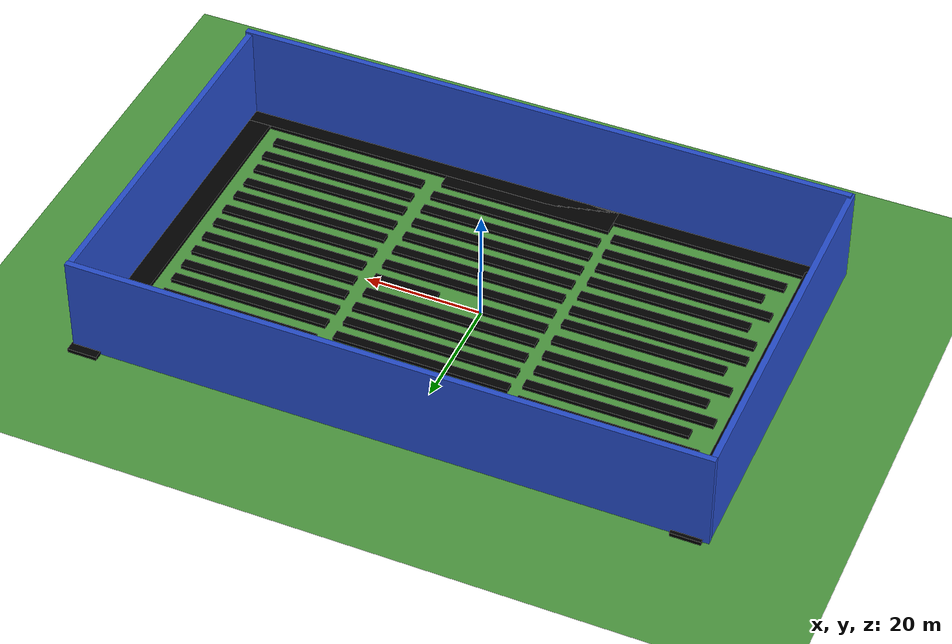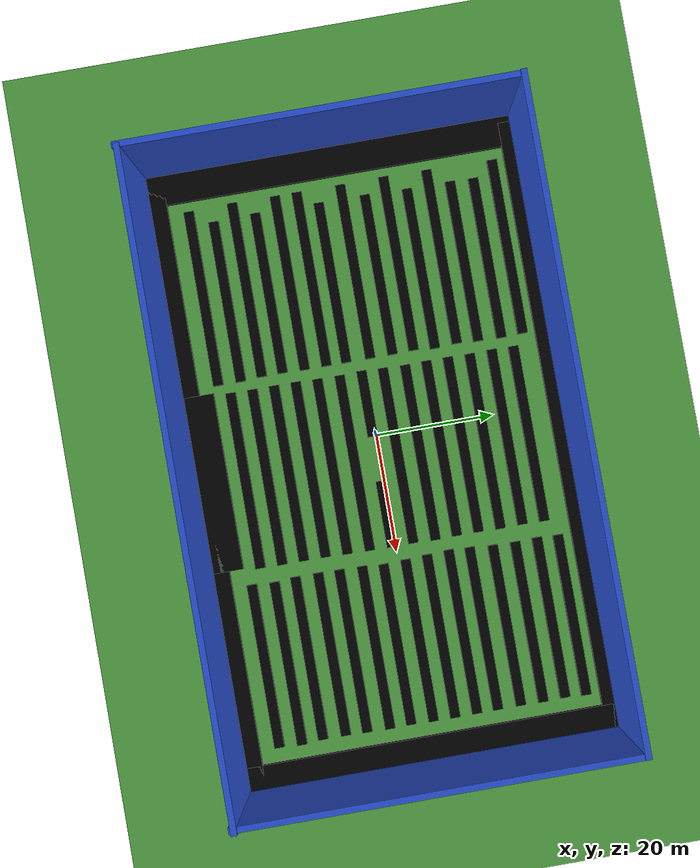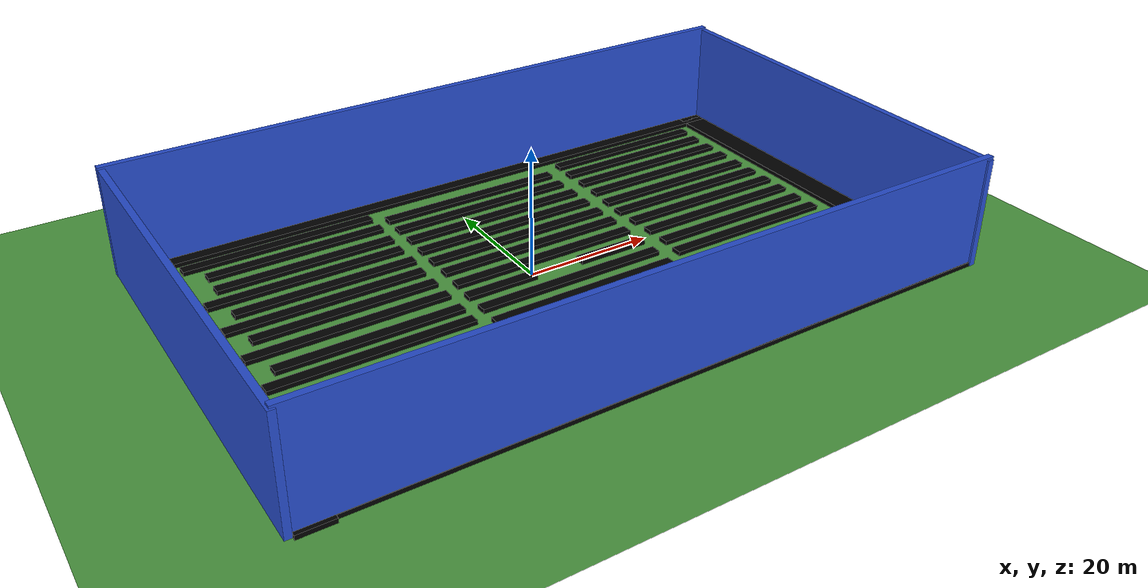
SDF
<sdf version="1.6">
 <world name="default">
  <light name="sun" type="directional">
   <pose>0 0 10 0 -0 0</pose>
   <diffuse>0.8 0.8 0.8 1</diffuse>
   <specular>0.1 0.1 0.1 1</specular>
   <attenuation>
    <range>1000</range>
    <constant>0.9</constant>
    <linear>0.01</linear>
    <quadratic>0.001</quadratic>
   </attenuation>
   <direction>-0.5 0.5 -1</direction>
  </light>
  <model name="ground_plane">
   <static>1</static>
   <link name="link">
    <collision name="collision">
     <geometry><plane><normal>0 0 1</normal><size>120 120</size></plane></geometry>
     <surface><friction><ode><mu>100</mu><mu2>50</mu2></ode></friction></surface>
    </collision>
    <visual name="visual">
     <cast_shadows>0</cast_shadows>
     <geometry><plane><normal>0 0 1</normal><size>120 120</size></plane></geometry>
     <material>
      <script><uri>file://media/materials/scripts/gazebo.material</uri><name>Gazebo/Grass</name></script>
     </material>
    </visual>
   </link>
  </model>
  <gravity>0 0 -9.8</gravity>
  <magnetic_field>6e-06 2.3e-05 -4.2e-05</magnetic_field>
  <atmosphere type="adiabatic"/>
  <physics name="default_physics" default="0" type="ode">
   <max_step_size>0.001</max_step_size>
   <real_time_factor>1</real_time_factor>
   <real_time_update_rate>1000</real_time_update_rate>
  </physics>
  <scene><ambient>0.4 0.4 0.4 1</ambient><background>0.7 0.7 0.7 1</background><shadows>1</shadows></scene>
  <spherical_coordinates>
   <surface_model>EARTH_WGS84</surface_model>
   <latitude_deg>0</latitude_deg>
   <longitude_deg>0</longitude_deg>
   <elevation>0</elevation>
   <heading_deg>0</heading_deg>
  </spherical_coordinates>
  <model name="crop_01_8">
   <link name="crop_01_0::link_0">
    <inertial>
     <mass>10.9148</mass>
     <inertia><ixx>13.7036</ixx><ixy>0</ixy><ixz>0</ixz><iyy>702.087</iyy><iyz>0</iyz><izz>715.772</izz></inertia>
    </inertial>
    <visual name="visual">
     <geometry><box><size>30 1.68705 1</size></box></geometry>
     <material>
      <ambient>0 1 0 1</ambient>
      <diffuse>0 0 0 1</diffuse>
      <specular>0.1 0.1 0.1 1</specular>
      <emissive>0 0 0 0</emissive>
     </material>
    </visual>
    <collision name="collision">
     <geometry><box><size>30 1.68705 1</size></box></geometry>
     <surface>
      <friction>
       <ode><mu>1</mu><mu2>1</mu2><fdir1>0 0 0</fdir1><slip1>0</slip1><slip2>0</slip2></ode>
       <torsional>
        <coefficient>1</coefficient>
        <patch_radius>0</patch_radius>
        <surface_radius>0</surface_radius>
        <use_patch_radius>1</use_patch_radius>
        <ode><slip>0</slip></ode>
       </torsional>
      </friction>
      <bounce><restitution_coefficient>0</restitution_coefficient><threshold>1e+06</threshold></bounce>
      <contact>
       <collide_without_contact>0</collide_without_contact>
       <collide_without_contact_bitmask>1</collide_without_contact_bitmask>
       <collide_bitmask>1</collide_bitmask>
       <ode>
        <soft_cfm>0</soft_cfm>
        <soft_erp>0.2</soft_erp>
        <kp>1e+13</kp>
        <kd>1</kd>
        <max_vel>0.01</max_vel>
        <min_depth>0</min_depth>
       </ode>
       <bullet>
        <split_impulse>1</split_impulse>
        <split_impulse_penetration_threshold>-0.01</split_impulse_penetration_threshold>
        <soft_cfm>0</soft_cfm>
        <soft_erp>0.2</soft_erp>
        <kp>1e+13</kp>
        <kd>1</kd>
       </bullet>
      </contact>
     </surface>
    </collision>
   </link>
   <static>1</static>
   <pose>3.80294 -11.8661 0.050638 0 -0 0</pose>
  </model>
  <model name="WALLS">
   <link name="link_0">
    <pose>-4.49328 -45.6418 8.05225 0 -0 0</pose>
    <inertial>
     <mass>1098.77</mass>
     <inertia><ixx>408732</ixx><ixy>0</ixy><ixz>0</ixz><iyy>26571.1</iyy><iyz>0</iyz><izz>382344</izz></inertia>
    </inertial>
    <visual name="visual">
     <geometry><box><size>1 64.6118 17.0056</size></box></geometry>
     <material>
      <script><uri>file://media/materials/scripts/gazebo.material</uri><name>Gazebo/BlueLaser</name></script>
     </material>
    </visual>
    <collision name="collision">
     <geometry><box><size>1 64.6118 17.0056</size></box></geometry>
     <surface>
      <friction>
       <ode><mu>1</mu><mu2>1</mu2><fdir1>0 0 0</fdir1><slip1>0</slip1><slip2>0</slip2></ode>
       <torsional>
        <coefficient>1</coefficient>
        <patch_radius>0</patch_radius>
        <surface_radius>0</surface_radius>
        <use_patch_radius>1</use_patch_radius>
        <ode><slip>0</slip></ode>
       </torsional>
      </friction>
      <bounce><restitution_coefficient>0</restitution_coefficient><threshold>1e+06</threshold></bounce>
      <contact>
       <collide_without_contact>0</collide_without_contact>
       <collide_without_contact_bitmask>1</collide_without_contact_bitmask>
       <collide_bitmask>1</collide_bitmask>
       <ode>
        <soft_cfm>0</soft_cfm>
        <soft_erp>0.2</soft_erp>
        <kp>1e+13</kp>
        <kd>1</kd>
        <max_vel>0.01</max_vel>
        <min_depth>0</min_depth>
       </ode>
       <bullet>
        <split_impulse>1</split_impulse>
        <split_impulse_penetration_threshold>-0.01</split_impulse_penetration_threshold>
        <soft_cfm>0</soft_cfm>
        <soft_erp>0.2</soft_erp>
        <kp>1e+13</kp>
        <kd>1</kd>
       </bullet>
      </contact>
     </surface>
    </collision>
   </link>
   <link name="link_0_clone">
    <pose>101.382 -45.6581 8.05225 0 -0 0</pose>
    <inertial>
     <mass>1098.77</mass>
     <inertia><ixx>408732</ixx><ixy>0</ixy><ixz>0</ixz><iyy>26571.1</iyy><iyz>0</iyz><izz>382344</izz></inertia>
    </inertial>
    <visual name="visual">
     <geometry><box><size>1 64.6118 17.0056</size></box></geometry>
     <material>
      <script><uri>file://media/materials/scripts/gazebo.material</uri><name>Gazebo/BlueLaser</name></script>
     </material>
    </visual>
    <collision name="collision">
     <geometry><box><size>1 64.6118 17.0056</size></box></geometry>
     <surface>
      <friction>
       <ode><mu>1</mu><mu2>1</mu2><fdir1>0 0 0</fdir1><slip1>0</slip1><slip2>0</slip2></ode>
       <torsional>
        <coefficient>1</coefficient>
        <patch_radius>0</patch_radius>
        <surface_radius>0</surface_radius>
        <use_patch_radius>1</use_patch_radius>
        <ode><slip>0</slip></ode>
       </torsional>
      </friction>
      <bounce><restitution_coefficient>0</restitution_coefficient><threshold>1e+06</threshold></bounce>
      <contact>
       <collide_without_contact>0</collide_without_contact>
       <collide_without_contact_bitmask>1</collide_without_contact_bitmask>
       <collide_bitmask>1</collide_bitmask>
       <ode>
        <soft_cfm>0</soft_cfm>
        <soft_erp>0.2</soft_erp>
        <kp>1e+13</kp>
        <kd>1</kd>
        <max_vel>0.01</max_vel>
        <min_depth>0</min_depth>
       </ode>
       <bullet>
        <split_impulse>1</split_impulse>
        <split_impulse_penetration_threshold>-0.01</split_impulse_penetration_threshold>
        <soft_cfm>0</soft_cfm>
        <soft_erp>0.2</soft_erp>
        <kp>1e+13</kp>
        <kd>1</kd>
       </bullet>
      </contact>
     </surface>
    </collision>
   </link>
   <link name="link_clone">
    <pose>48.7455 -77.1551 8.20614 0 -0 0</pose>
    <inertial>
     <mass>1851.31</mass>
     <inertia>
      <ixx>46490.6</ixx>
      <ixy>0</ixy>
      <ixz>0</ixz>
      <iyy>1.80683e+06</iyy>
      <iyz>0</iyz>
      <izz>1.76065e+06</izz>
     </inertia>
    </inertial>
    <visual name="visual">
     <geometry><box><size>106.824 1 17.3306</size></box></geometry>
     <material>
      <script><uri>file://media/materials/scripts/gazebo.material</uri><name>Gazebo/BlueLaser</name></script>
     </material>
    </visual>
    <collision name="collision">
     <geometry><box><size>106.824 1 17.3306</size></box></geometry>
     <surface>
      <friction>
       <ode><mu>1</mu><mu2>1</mu2><fdir1>0 0 0</fdir1><slip1>0</slip1><slip2>0</slip2></ode>
       <torsional>
        <coefficient>1</coefficient>
        <patch_radius>0</patch_radius>
        <surface_radius>0</surface_radius>
        <use_patch_radius>1</use_patch_radius>
        <ode><slip>0</slip></ode>
       </torsional>
      </friction>
      <bounce><restitution_coefficient>0</restitution_coefficient><threshold>1e+06</threshold></bounce>
      <contact>
       <collide_without_contact>0</collide_without_contact>
       <collide_without_contact_bitmask>1</collide_without_contact_bitmask>
       <collide_bitmask>1</collide_bitmask>
       <ode>
        <soft_cfm>0</soft_cfm>
        <soft_erp>0.2</soft_erp>
        <kp>1e+13</kp>
        <kd>1</kd>
        <max_vel>0.01</max_vel>
        <min_depth>0</min_depth>
       </ode>
       <bullet>
        <split_impulse>1</split_impulse>
        <split_impulse_penetration_threshold>-0.01</split_impulse_penetration_threshold>
        <soft_cfm>0</soft_cfm>
        <soft_erp>0.2</soft_erp>
        <kp>1e+13</kp>
        <kd>1</kd>
       </bullet>
      </contact>
     </surface>
    </collision>
   </link>
   <link name="link_clone_clone">
    <pose>48.3822 -13.6581 8.20614 0 -0 0</pose>
    <inertial>
     <mass>1851.31</mass>
     <inertia>
      <ixx>46490.6</ixx>
      <ixy>0</ixy>
      <ixz>0</ixz>
      <iyy>1.80683e+06</iyy>
      <iyz>0</iyz>
      <izz>1.76065e+06</izz>
     </inertia>
    </inertial>
    <visual name="visual">
     <geometry><box><size>106.824 1 17.3306</size></box></geometry>
     <material>
      <script><uri>file://media/materials/scripts/gazebo.material</uri><name>Gazebo/BlueLaser</name></script>
     </material>
    </visual>
    <collision name="collision">
     <geometry><box><size>106.824 1 17.3306</size></box></geometry>
     <surface>
      <friction>
       <ode><mu>1</mu><mu2>1</mu2><fdir1>0 0 0</fdir1><slip1>0</slip1><slip2>0</slip2></ode>
       <torsional>
        <coefficient>1</coefficient>
        <patch_radius>0</patch_radius>
        <surface_radius>0</surface_radius>
        <use_patch_radius>1</use_patch_radius>
        <ode><slip>0</slip></ode>
       </torsional>
      </friction>
      <bounce><restitution_coefficient>0</restitution_coefficient><threshold>1e+06</threshold></bounce>
      <contact>
       <collide_without_contact>0</collide_without_contact>
       <collide_without_contact_bitmask>1</collide_without_contact_bitmask>
       <collide_bitmask>1</collide_bitmask>
       <ode>
        <soft_cfm>0</soft_cfm>
        <soft_erp>0.2</soft_erp>
        <kp>1e+13</kp>
        <kd>1</kd>
        <max_vel>0.01</max_vel>
        <min_depth>0</min_depth>
       </ode>
       <bullet>
        <split_impulse>1</split_impulse>
        <split_impulse_penetration_threshold>-0.01</split_impulse_penetration_threshold>
        <soft_cfm>0</soft_cfm>
        <soft_erp>0.2</soft_erp>
        <kp>1e+13</kp>
        <kd>1</kd>
       </bullet>
      </contact>
     </surface>
    </collision>
   </link>
   <static>1</static>
   <pose>-45.7442 45.6641 0.450532 0 -0 0.000945</pose>
  </model>
  <model name="crop_01_8_clone">
   <link name="crop_01_0::link_0">
    <inertial>
     <mass>10.9148</mass>
     <inertia><ixx>13.7036</ixx><ixy>0</ixy><ixz>0</ixz><iyy>702.087</iyy><iyz>0</iyz><izz>715.772</izz></inertia>
    </inertial>
    <visual name="visual">
     <geometry><box><size>30 1.68705 1</size></box></geometry>
     <material>
      <ambient>0 1 0 1</ambient>
      <diffuse>0 0 0 1</diffuse>
      <specular>0.1 0.1 0.1 1</specular>
      <emissive>0 0 0 0</emissive>
     </material>
    </visual>
    <collision name="collision">
     <geometry><box><size>30 1.68705 1</size></box></geometry>
     <surface>
      <friction>
       <ode><mu>1</mu><mu2>1</mu2><fdir1>0 0 0</fdir1><slip1>0</slip1><slip2>0</slip2></ode>
       <torsional>
        <coefficient>1</coefficient>
        <patch_radius>0</patch_radius>
        <surface_radius>0</surface_radius>
        <use_patch_radius>1</use_patch_radius>
        <ode><slip>0</slip></ode>
       </torsional>
      </friction>
      <bounce><restitution_coefficient>0</restitution_coefficient><threshold>1e+06</threshold></bounce>
      <contact>
       <collide_without_contact>0</collide_without_contact>
       <collide_without_contact_bitmask>1</collide_without_contact_bitmask>
       <collide_bitmask>1</collide_bitmask>
       <ode>
        <soft_cfm>0</soft_cfm>
        <soft_erp>0.2</soft_erp>
        <kp>1e+13</kp>
        <kd>1</kd>
        <max_vel>0.01</max_vel>
        <min_depth>0</min_depth>
       </ode>
       <bullet>
        <split_impulse>1</split_impulse>
        <split_impulse_penetration_threshold>-0.01</split_impulse_penetration_threshold>
        <soft_cfm>0</soft_cfm>
        <soft_erp>0.2</soft_erp>
        <kp>1e+13</kp>
        <kd>1</kd>
       </bullet>
      </contact>
     </surface>
    </collision>
   </link>
   <static>1</static>
   <pose>3.79308 -15.5752 0.050638 0 -0 0</pose>
  </model>
  <model name="crop_01_8_clone_0">
   <link name="crop_01_0::link_0">
    <inertial>
     <mass>10.9148</mass>
     <inertia><ixx>13.7036</ixx><ixy>0</ixy><ixz>0</ixz><iyy>702.087</iyy><iyz>0</iyz><izz>715.772</izz></inertia>
    </inertial>
    <visual name="visual">
     <geometry><box><size>30 1.68705 1</size></box></geometry>
     <material>
      <ambient>0 1 0 1</ambient>
      <diffuse>0 0 0 1</diffuse>
      <specular>0.1 0.1 0.1 1</specular>
      <emissive>0 0 0 0</emissive>
     </material>
    </visual>
    <collision name="collision">
     <geometry><box><size>30 1.68705 1</size></box></geometry>
     <surface>
      <friction>
       <ode><mu>1</mu><mu2>1</mu2><fdir1>0 0 0</fdir1><slip1>0</slip1><slip2>0</slip2></ode>
       <torsional>
        <coefficient>1</coefficient>
        <patch_radius>0</patch_radius>
        <surface_radius>0</surface_radius>
        <use_patch_radius>1</use_patch_radius>
        <ode><slip>0</slip></ode>
       </torsional>
      </friction>
      <bounce><restitution_coefficient>0</restitution_coefficient><threshold>1e+06</threshold></bounce>
      <contact>
       <collide_without_contact>0</collide_without_contact>
       <collide_without_contact_bitmask>1</collide_without_contact_bitmask>
       <collide_bitmask>1</collide_bitmask>
       <ode>
        <soft_cfm>0</soft_cfm>
        <soft_erp>0.2</soft_erp>
        <kp>1e+13</kp>
        <kd>1</kd>
        <max_vel>0.01</max_vel>
        <min_depth>0</min_depth>
       </ode>
       <bullet>
        <split_impulse>1</split_impulse>
        <split_impulse_penetration_threshold>-0.01</split_impulse_penetration_threshold>
        <soft_cfm>0</soft_cfm>
        <soft_erp>0.2</soft_erp>
        <kp>1e+13</kp>
        <kd>1</kd>
       </bullet>
      </contact>
     </surface>
    </collision>
   </link>
   <static>1</static>
   <pose>3.92731 -8.15154 0.050638 0 -0 0</pose>
  </model>
  <model name="crop_01_8_clone_0_clone_0_clone">
   <link name="crop_01_0::link_0">
    <inertial>
     <mass>10.9148</mass>
     <inertia><ixx>13.7036</ixx><ixy>0</ixy><ixz>0</ixz><iyy>702.087</iyy><iyz>0</iyz><izz>715.772</izz></inertia>
    </inertial>
    <visual name="visual">
     <geometry><box><size>11.274 1.68705 1</size></box></geometry>
     <material>
      <ambient>0 1 0 1</ambient>
      <diffuse>0 0 0 1</diffuse>
      <specular>0.1 0.1 0.1 1</specular>
      <emissive>0 0 0 0</emissive>
     </material>
    </visual>
    <collision name="collision">
     <geometry><box><size>11.274 1.68705 1</size></box></geometry>
     <surface>
      <friction>
       <ode><mu>1</mu><mu2>1</mu2><fdir1>0 0 0</fdir1><slip1>0</slip1><slip2>0</slip2></ode>
       <torsional>
        <coefficient>1</coefficient>
        <patch_radius>0</patch_radius>
        <surface_radius>0</surface_radius>
        <use_patch_radius>1</use_patch_radius>
        <ode><slip>0</slip></ode>
       </torsional>
      </friction>
      <bounce><restitution_coefficient>0</restitution_coefficient><threshold>1e+06</threshold></bounce>
      <contact>
       <collide_without_contact>0</collide_without_contact>
       <collide_without_contact_bitmask>1</collide_without_contact_bitmask>
       <collide_bitmask>1</collide_bitmask>
       <ode>
        <soft_cfm>0</soft_cfm>
        <soft_erp>0.2</soft_erp>
        <kp>1e+13</kp>
        <kd>1</kd>
        <max_vel>0.01</max_vel>
        <min_depth>0</min_depth>
       </ode>
       <bullet>
        <split_impulse>1</split_impulse>
        <split_impulse_penetration_threshold>-0.01</split_impulse_penetration_threshold>
        <soft_cfm>0</soft_cfm>
        <soft_erp>0.2</soft_erp>
        <kp>1e+13</kp>
        <kd>1</kd>
       </bullet>
      </contact>
     </surface>
    </collision>
   </link>
   <static>1</static>
   <pose>-5.5065 -0.57479 0.050638 0 -0 0</pose>
  </model>
  <model name="crop_01_8_clone_0_clone_0_clone_0">
   <link name="crop_01_0::link_0">
    <inertial>
     <mass>10.9148</mass>
     <inertia><ixx>13.7036</ixx><ixy>0</ixy><ixz>0</ixz><iyy>702.087</iyy><iyz>0</iyz><izz>715.772</izz></inertia>
    </inertial>
    <visual name="visual">
     <geometry><box><size>30 1.68705 1</size></box></geometry>
     <material>
      <ambient>0 1 0 1</ambient>
      <diffuse>0 0 0 1</diffuse>
      <specular>0.1 0.1 0.1 1</specular>
      <emissive>0 0 0 0</emissive>
     </material>
    </visual>
    <collision name="collision">
     <geometry><box><size>30 1.68705 1</size></box></geometry>
     <surface>
      <friction>
       <ode><mu>1</mu><mu2>1</mu2><fdir1>0 0 0</fdir1><slip1>0</slip1><slip2>0</slip2></ode>
       <torsional>
        <coefficient>1</coefficient>
        <patch_radius>0</patch_radius>
        <surface_radius>0</surface_radius>
        <use_patch_radius>1</use_patch_radius>
        <ode><slip>0</slip></ode>
       </torsional>
      </friction>
      <bounce><restitution_coefficient>0</restitution_coefficient><threshold>1e+06</threshold></bounce>
      <contact>
       <collide_without_contact>0</collide_without_contact>
       <collide_without_contact_bitmask>1</collide_without_contact_bitmask>
       <collide_bitmask>1</collide_bitmask>
       <ode>
        <soft_cfm>0</soft_cfm>
        <soft_erp>0.2</soft_erp>
        <kp>1e+13</kp>
        <kd>1</kd>
        <max_vel>0.01</max_vel>
        <min_depth>0</min_depth>
       </ode>
       <bullet>
        <split_impulse>1</split_impulse>
        <split_impulse_penetration_threshold>-0.01</split_impulse_penetration_threshold>
        <soft_cfm>0</soft_cfm>
        <soft_erp>0.2</soft_erp>
        <kp>1e+13</kp>
        <kd>1</kd>
       </bullet>
      </contact>
     </surface>
    </collision>
   </link>
   <static>1</static>
   <pose>4.01911 3.07059 0.050638 0 -0 0</pose>
  </model>
  <model name="crop_01_8_clone_0_clone_0_clone_1">
   <link name="crop_01_0::link_0">
    <inertial>
     <mass>10.9148</mass>
     <inertia><ixx>13.7036</ixx><ixy>0</ixy><ixz>0</ixz><iyy>702.087</iyy><iyz>0</iyz><izz>715.772</izz></inertia>
    </inertial>
    <visual name="visual">
     <geometry><box><size>30 1.68705 1</size></box></geometry>
     <material>
      <ambient>0 1 0 1</ambient>
      <diffuse>0 0 0 1</diffuse>
      <specular>0.1 0.1 0.1 1</specular>
      <emissive>0 0 0 0</emissive>
     </material>
    </visual>
    <collision name="collision">
     <geometry><box><size>30 1.68705 1</size></box></geometry>
     <surface>
      <friction>
       <ode><mu>1</mu><mu2>1</mu2><fdir1>0 0 0</fdir1><slip1>0</slip1><slip2>0</slip2></ode>
       <torsional>
        <coefficient>1</coefficient>
        <patch_radius>0</patch_radius>
        <surface_radius>0</surface_radius>
        <use_patch_radius>1</use_patch_radius>
        <ode><slip>0</slip></ode>
       </torsional>
      </friction>
      <bounce><restitution_coefficient>0</restitution_coefficient><threshold>1e+06</threshold></bounce>
      <contact>
       <collide_without_contact>0</collide_without_contact>
       <collide_without_contact_bitmask>1</collide_without_contact_bitmask>
       <collide_bitmask>1</collide_bitmask>
       <ode>
        <soft_cfm>0</soft_cfm>
        <soft_erp>0.2</soft_erp>
        <kp>1e+13</kp>
        <kd>1</kd>
        <max_vel>0.01</max_vel>
        <min_depth>0</min_depth>
       </ode>
       <bullet>
        <split_impulse>1</split_impulse>
        <split_impulse_penetration_threshold>-0.01</split_impulse_penetration_threshold>
        <soft_cfm>0</soft_cfm>
        <soft_erp>0.2</soft_erp>
        <kp>1e+13</kp>
        <kd>1</kd>
       </bullet>
      </contact>
     </surface>
    </collision>
   </link>
   <static>1</static>
   <pose>4.14547 6.85606 0.050638 0 -0 0</pose>
  </model>
  <model name="crop_01_8_clone_0_clone_0_clone_1_clone_clone">
   <link name="crop_01_0::link_0">
    <inertial>
     <mass>10.9148</mass>
     <inertia><ixx>13.7036</ixx><ixy>0</ixy><ixz>0</ixz><iyy>702.087</iyy><iyz>0</iyz><izz>715.772</izz></inertia>
    </inertial>
    <visual name="visual">
     <geometry><box><size>30 1.68705 1</size></box></geometry>
     <material>
      <ambient>0 1 0 1</ambient>
      <diffuse>0 0 0 1</diffuse>
      <specular>0.1 0.1 0.1 1</specular>
      <emissive>0 0 0 0</emissive>
     </material>
    </visual>
    <collision name="collision">
     <geometry><box><size>30 1.68705 1</size></box></geometry>
     <surface>
      <friction>
       <ode><mu>1</mu><mu2>1</mu2><fdir1>0 0 0</fdir1><slip1>0</slip1><slip2>0</slip2></ode>
       <torsional>
        <coefficient>1</coefficient>
        <patch_radius>0</patch_radius>
        <surface_radius>0</surface_radius>
        <use_patch_radius>1</use_patch_radius>
        <ode><slip>0</slip></ode>
       </torsional>
      </friction>
      <bounce><restitution_coefficient>0</restitution_coefficient><threshold>1e+06</threshold></bounce>
      <contact>
       <collide_without_contact>0</collide_without_contact>
       <collide_without_contact_bitmask>1</collide_without_contact_bitmask>
       <collide_bitmask>1</collide_bitmask>
       <ode>
        <soft_cfm>0</soft_cfm>
        <soft_erp>0.2</soft_erp>
        <kp>1e+13</kp>
        <kd>1</kd>
        <max_vel>0.01</max_vel>
        <min_depth>0</min_depth>
       </ode>
       <bullet>
        <split_impulse>1</split_impulse>
        <split_impulse_penetration_threshold>-0.01</split_impulse_penetration_threshold>
        <soft_cfm>0</soft_cfm>
        <soft_erp>0.2</soft_erp>
        <kp>1e+13</kp>
        <kd>1</kd>
       </bullet>
      </contact>
     </surface>
    </collision>
   </link>
   <static>1</static>
   <pose>4.07189 10.5095 0.050638 0 -0 0</pose>
  </model>
  <model name="crop_01_8_clone_0_clone_0_clone_1_clone_clone_clone">
   <link name="crop_01_0::link_0">
    <inertial>
     <mass>10.9148</mass>
     <inertia><ixx>13.7036</ixx><ixy>0</ixy><ixz>0</ixz><iyy>702.087</iyy><iyz>0</iyz><izz>715.772</izz></inertia>
    </inertial>
    <visual name="visual">
     <geometry><box><size>30 1.68705 1</size></box></geometry>
     <material>
      <ambient>0 1 0 1</ambient>
      <diffuse>0 0 0 1</diffuse>
      <specular>0.1 0.1 0.1 1</specular>
      <emissive>0 0 0 0</emissive>
     </material>
    </visual>
    <collision name="collision">
     <geometry><box><size>30 1.68705 1</size></box></geometry>
     <surface>
      <friction>
       <ode><mu>1</mu><mu2>1</mu2><fdir1>0 0 0</fdir1><slip1>0</slip1><slip2>0</slip2></ode>
       <torsional>
        <coefficient>1</coefficient>
        <patch_radius>0</patch_radius>
        <surface_radius>0</surface_radius>
        <use_patch_radius>1</use_patch_radius>
        <ode><slip>0</slip></ode>
       </torsional>
      </friction>
      <bounce><restitution_coefficient>0</restitution_coefficient><threshold>1e+06</threshold></bounce>
      <contact>
       <collide_without_contact>0</collide_without_contact>
       <collide_without_contact_bitmask>1</collide_without_contact_bitmask>
       <collide_bitmask>1</collide_bitmask>
       <ode>
        <soft_cfm>0</soft_cfm>
        <soft_erp>0.2</soft_erp>
        <kp>1e+13</kp>
        <kd>1</kd>
        <max_vel>0.01</max_vel>
        <min_depth>0</min_depth>
       </ode>
       <bullet>
        <split_impulse>1</split_impulse>
        <split_impulse_penetration_threshold>-0.01</split_impulse_penetration_threshold>
        <soft_cfm>0</soft_cfm>
        <soft_erp>0.2</soft_erp>
        <kp>1e+13</kp>
        <kd>1</kd>
       </bullet>
      </contact>
     </surface>
    </collision>
   </link>
   <static>1</static>
   <pose>4.07232 14.2098 0.050638 0 -0 0</pose>
  </model>
  <model name="crop_01_8_clone_0_clone_0_clone_1_clone_clone_clone_clone">
   <link name="crop_01_0::link_0">
    <inertial>
     <mass>10.9148</mass>
     <inertia><ixx>13.7036</ixx><ixy>0</ixy><ixz>0</ixz><iyy>702.087</iyy><iyz>0</iyz><izz>715.772</izz></inertia>
    </inertial>
    <visual name="visual">
     <geometry><box><size>30 1.68705 1</size></box></geometry>
     <material>
      <ambient>0 1 0 1</ambient>
      <diffuse>0 0 0 1</diffuse>
      <specular>0.1 0.1 0.1 1</specular>
      <emissive>0 0 0 0</emissive>
     </material>
    </visual>
    <collision name="collision">
     <geometry><box><size>30 1.68705 1</size></box></geometry>
     <surface>
      <friction>
       <ode><mu>1</mu><mu2>1</mu2><fdir1>0 0 0</fdir1><slip1>0</slip1><slip2>0</slip2></ode>
       <torsional>
        <coefficient>1</coefficient>
        <patch_radius>0</patch_radius>
        <surface_radius>0</surface_radius>
        <use_patch_radius>1</use_patch_radius>
        <ode><slip>0</slip></ode>
       </torsional>
      </friction>
      <bounce><restitution_coefficient>0</restitution_coefficient><threshold>1e+06</threshold></bounce>
      <contact>
       <collide_without_contact>0</collide_without_contact>
       <collide_without_contact_bitmask>1</collide_without_contact_bitmask>
       <collide_bitmask>1</collide_bitmask>
       <ode>
        <soft_cfm>0</soft_cfm>
        <soft_erp>0.2</soft_erp>
        <kp>1e+13</kp>
        <kd>1</kd>
        <max_vel>0.01</max_vel>
        <min_depth>0</min_depth>
       </ode>
       <bullet>
        <split_impulse>1</split_impulse>
        <split_impulse_penetration_threshold>-0.01</split_impulse_penetration_threshold>
        <soft_cfm>0</soft_cfm>
        <soft_erp>0.2</soft_erp>
        <kp>1e+13</kp>
        <kd>1</kd>
       </bullet>
      </contact>
     </surface>
    </collision>
   </link>
   <static>1</static>
   <pose>4.16243 17.9486 0.050638 0 -0 0</pose>
  </model>
  <model name="crop_01_8_clone_0_clone_0_clone_1_clone_clone_clone_clone_0">
   <link name="crop_01_0::link_0">
    <inertial>
     <mass>10.9148</mass>
     <inertia><ixx>13.7036</ixx><ixy>0</ixy><ixz>0</ixz><iyy>702.087</iyy><iyz>0</iyz><izz>715.772</izz></inertia>
    </inertial>
    <visual name="visual">
     <geometry><box><size>30 1.68705 1</size></box></geometry>
     <material>
      <ambient>0 1 0 1</ambient>
      <diffuse>0 0 0 1</diffuse>
      <specular>0.1 0.1 0.1 1</specular>
      <emissive>0 0 0 0</emissive>
     </material>
    </visual>
    <collision name="collision">
     <geometry><box><size>30 1.68705 1</size></box></geometry>
     <surface>
      <friction>
       <ode><mu>1</mu><mu2>1</mu2><fdir1>0 0 0</fdir1><slip1>0</slip1><slip2>0</slip2></ode>
       <torsional>
        <coefficient>1</coefficient>
        <patch_radius>0</patch_radius>
        <surface_radius>0</surface_radius>
        <use_patch_radius>1</use_patch_radius>
        <ode><slip>0</slip></ode>
       </torsional>
      </friction>
      <bounce><restitution_coefficient>0</restitution_coefficient><threshold>1e+06</threshold></bounce>
      <contact>
       <collide_without_contact>0</collide_without_contact>
       <collide_without_contact_bitmask>1</collide_without_contact_bitmask>
       <collide_bitmask>1</collide_bitmask>
       <ode>
        <soft_cfm>0</soft_cfm>
        <soft_erp>0.2</soft_erp>
        <kp>1e+13</kp>
        <kd>1</kd>
        <max_vel>0.01</max_vel>
        <min_depth>0</min_depth>
       </ode>
       <bullet>
        <split_impulse>1</split_impulse>
        <split_impulse_penetration_threshold>-0.01</split_impulse_penetration_threshold>
        <soft_cfm>0</soft_cfm>
        <soft_erp>0.2</soft_erp>
        <kp>1e+13</kp>
        <kd>1</kd>
       </bullet>
      </contact>
     </surface>
    </collision>
   </link>
   <static>1</static>
   <pose>4.08383 21.7323 0.050638 0 -0 0</pose>
  </model>
  <model name="crop_01_8_clone_0_clone_0_clone_1_clone_clone_clone_clone_0_clone">
   <link name="crop_01_0::link_0">
    <inertial>
     <mass>10.9148</mass>
     <inertia><ixx>13.7036</ixx><ixy>0</ixy><ixz>0</ixz><iyy>702.087</iyy><iyz>0</iyz><izz>715.772</izz></inertia>
    </inertial>
    <visual name="visual">
     <geometry><box><size>30 1.68705 1</size></box></geometry>
     <material>
      <ambient>0 1 0 1</ambient>
      <diffuse>0 0 0 1</diffuse>
      <specular>0.1 0.1 0.1 1</specular>
      <emissive>0 0 0 0</emissive>
     </material>
    </visual>
    <collision name="collision">
     <geometry><box><size>30 1.68705 1</size></box></geometry>
     <surface>
      <friction>
       <ode><mu>1</mu><mu2>1</mu2><fdir1>0 0 0</fdir1><slip1>0</slip1><slip2>0</slip2></ode>
       <torsional>
        <coefficient>1</coefficient>
        <patch_radius>0</patch_radius>
        <surface_radius>0</surface_radius>
        <use_patch_radius>1</use_patch_radius>
        <ode><slip>0</slip></ode>
       </torsional>
      </friction>
      <bounce><restitution_coefficient>0</restitution_coefficient><threshold>1e+06</threshold></bounce>
      <contact>
       <collide_without_contact>0</collide_without_contact>
       <collide_without_contact_bitmask>1</collide_without_contact_bitmask>
       <collide_bitmask>1</collide_bitmask>
       <ode>
        <soft_cfm>0</soft_cfm>
        <soft_erp>0.2</soft_erp>
        <kp>1e+13</kp>
        <kd>1</kd>
        <max_vel>0.01</max_vel>
        <min_depth>0</min_depth>
       </ode>
       <bullet>
        <split_impulse>1</split_impulse>
        <split_impulse_penetration_threshold>-0.01</split_impulse_penetration_threshold>
        <soft_cfm>0</soft_cfm>
        <soft_erp>0.2</soft_erp>
        <kp>1e+13</kp>
        <kd>1</kd>
       </bullet>
      </contact>
     </surface>
    </collision>
   </link>
   <static>1</static>
   <pose>4.15605 25.4436 0.050638 0 -0 0</pose>
  </model>
  <model name="crop_01_8_clone_0_clone_0_clone_1_clone_clone_clone_clone_0_clone_0">
   <link name="crop_01_0::link_0">
    <inertial>
     <mass>10.9148</mass>
     <inertia><ixx>13.7036</ixx><ixy>0</ixy><ixz>0</ixz><iyy>702.087</iyy><iyz>0</iyz><izz>715.772</izz></inertia>
    </inertial>
    <visual name="visual">
     <geometry><box><size>105.069 2.60686 1</size></box></geometry>
     <material>
      <ambient>0 1 0 1</ambient>
      <diffuse>0 0 0 1</diffuse>
      <specular>0.1 0.1 0.1 1</specular>
      <emissive>0 0 0 0</emissive>
     </material>
    </visual>
    <collision name="collision">
     <geometry><box><size>105.069 2.60686 1</size></box></geometry>
     <surface>
      <friction>
       <ode><mu>1</mu><mu2>1</mu2><fdir1>0 0 0</fdir1><slip1>0</slip1><slip2>0</slip2></ode>
       <torsional>
        <coefficient>1</coefficient>
        <patch_radius>0</patch_radius>
        <surface_radius>0</surface_radius>
        <use_patch_radius>1</use_patch_radius>
        <ode><slip>0</slip></ode>
       </torsional>
      </friction>
      <bounce><restitution_coefficient>0</restitution_coefficient><threshold>1e+06</threshold></bounce>
      <contact>
       <collide_without_contact>0</collide_without_contact>
       <collide_without_contact_bitmask>1</collide_without_contact_bitmask>
       <collide_bitmask>1</collide_bitmask>
       <ode>
        <soft_cfm>0</soft_cfm>
        <soft_erp>0.2</soft_erp>
        <kp>1e+13</kp>
        <kd>1</kd>
        <max_vel>0.01</max_vel>
        <min_depth>0</min_depth>
       </ode>
       <bullet>
        <split_impulse>1</split_impulse>
        <split_impulse_penetration_threshold>-0.01</split_impulse_penetration_threshold>
        <soft_cfm>0</soft_cfm>
        <soft_erp>0.2</soft_erp>
        <kp>1e+13</kp>
        <kd>1</kd>
       </bullet>
      </contact>
     </surface>
    </collision>
   </link>
   <static>1</static>
   <pose>3.83873 30.826 0.050638 0 -0 0</pose>
  </model>
  <model name="crop_01_8_clone_0_clone_0_clone_1_clone_clone_clone_clone_0_clone_1">
   <link name="crop_01_0::link_0">
    <inertial>
     <mass>10.9148</mass>
     <inertia><ixx>13.7036</ixx><ixy>0</ixy><ixz>0</ixz><iyy>702.087</iyy><iyz>0</iyz><izz>715.772</izz></inertia>
    </inertial>
    <visual name="visual">
     <geometry><box><size>30 1.68705 1</size></box></geometry>
     <material>
      <ambient>0 1 0 1</ambient>
      <diffuse>0 0 0 1</diffuse>
      <specular>0.1 0.1 0.1 1</specular>
      <emissive>0 0 0 0</emissive>
     </material>
    </visual>
    <collision name="collision">
     <geometry><box><size>30 1.68705 1</size></box></geometry>
     <surface>
      <friction>
       <ode><mu>1</mu><mu2>1</mu2><fdir1>0 0 0</fdir1><slip1>0</slip1><slip2>0</slip2></ode>
       <torsional>
        <coefficient>1</coefficient>
        <patch_radius>0</patch_radius>
        <surface_radius>0</surface_radius>
        <use_patch_radius>1</use_patch_radius>
        <ode><slip>0</slip></ode>
       </torsional>
      </friction>
      <bounce><restitution_coefficient>0</restitution_coefficient><threshold>1e+06</threshold></bounce>
      <contact>
       <collide_without_contact>0</collide_without_contact>
       <collide_without_contact_bitmask>1</collide_without_contact_bitmask>
       <collide_bitmask>1</collide_bitmask>
       <ode>
        <soft_cfm>0</soft_cfm>
        <soft_erp>0.2</soft_erp>
        <kp>1e+13</kp>
        <kd>1</kd>
        <max_vel>0.01</max_vel>
        <min_depth>0</min_depth>
       </ode>
       <bullet>
        <split_impulse>1</split_impulse>
        <split_impulse_penetration_threshold>-0.01</split_impulse_penetration_threshold>
        <soft_cfm>0</soft_cfm>
        <soft_erp>0.2</soft_erp>
        <kp>1e+13</kp>
        <kd>1</kd>
       </bullet>
      </contact>
     </surface>
    </collision>
   </link>
   <static>1</static>
   <pose>3.80036 -19.2787 0.050638 0 -0 0</pose>
  </model>
  <model name="crop_01_8_clone_0_clone_0_clone_1_clone_clone_clone_clone_0_clone_3">
   <link name="crop_01_0::link_0">
    <inertial>
     <mass>10.9148</mass>
     <inertia><ixx>13.7036</ixx><ixy>0</ixy><ixz>0</ixz><iyy>702.087</iyy><iyz>0</iyz><izz>715.772</izz></inertia>
    </inertial>
    <visual name="visual">
     <geometry><box><size>30 1.68705 1</size></box></geometry>
     <material>
      <ambient>0 1 0 1</ambient>
      <diffuse>0 0 0 1</diffuse>
      <specular>0.1 0.1 0.1 1</specular>
      <emissive>0 0 0 0</emissive>
     </material>
    </visual>
    <collision name="collision">
     <geometry><box><size>30 1.68705 1</size></box></geometry>
     <surface>
      <friction>
       <ode><mu>1</mu><mu2>1</mu2><fdir1>0 0 0</fdir1><slip1>0</slip1><slip2>0</slip2></ode>
       <torsional>
        <coefficient>1</coefficient>
        <patch_radius>0</patch_radius>
        <surface_radius>0</surface_radius>
        <use_patch_radius>1</use_patch_radius>
        <ode><slip>0</slip></ode>
       </torsional>
      </friction>
      <bounce><restitution_coefficient>0</restitution_coefficient><threshold>1e+06</threshold></bounce>
      <contact>
       <collide_without_contact>0</collide_without_contact>
       <collide_without_contact_bitmask>1</collide_without_contact_bitmask>
       <collide_bitmask>1</collide_bitmask>
       <ode>
        <soft_cfm>0</soft_cfm>
        <soft_erp>0.2</soft_erp>
        <kp>1e+13</kp>
        <kd>1</kd>
        <max_vel>0.01</max_vel>
        <min_depth>0</min_depth>
       </ode>
       <bullet>
        <split_impulse>1</split_impulse>
        <split_impulse_penetration_threshold>-0.01</split_impulse_penetration_threshold>
        <soft_cfm>0</soft_cfm>
        <soft_erp>0.2</soft_erp>
        <kp>1e+13</kp>
        <kd>1</kd>
       </bullet>
      </contact>
     </surface>
    </collision>
   </link>
   <static>1</static>
   <pose>3.74697 -23.0068 0.050638 0 -0 0</pose>
  </model>
  <model name="crop_01_8_clone_0_clone_0_clone_1_clone_clone_clone_clone_0_clone_14">
   <link name="crop_01_0::link_0">
    <inertial>
     <mass>10.9148</mass>
     <inertia><ixx>13.7036</ixx><ixy>0</ixy><ixz>0</ixz><iyy>702.087</iyy><iyz>0</iyz><izz>715.772</izz></inertia>
    </inertial>
    <visual name="visual">
     <geometry><box><size>27.2326 1.68705 1</size></box></geometry>
     <material>
      <ambient>0 1 0 1</ambient>
      <diffuse>0 0 0 1</diffuse>
      <specular>0.1 0.1 0.1 1</specular>
      <emissive>0 0 0 0</emissive>
     </material>
    </visual>
    <collision name="collision">
     <geometry><box><size>27.2326 1.68705 1</size></box></geometry>
     <surface>
      <friction>
       <ode><mu>1</mu><mu2>1</mu2><fdir1>0 0 0</fdir1><slip1>0</slip1><slip2>0</slip2></ode>
       <torsional>
        <coefficient>1</coefficient>
        <patch_radius>0</patch_radius>
        <surface_radius>0</surface_radius>
        <use_patch_radius>1</use_patch_radius>
        <ode><slip>0</slip></ode>
       </torsional>
      </friction>
      <bounce><restitution_coefficient>0</restitution_coefficient><threshold>1e+06</threshold></bounce>
      <contact>
       <collide_without_contact>0</collide_without_contact>
       <collide_without_contact_bitmask>1</collide_without_contact_bitmask>
       <collide_bitmask>1</collide_bitmask>
       <ode>
        <soft_cfm>0</soft_cfm>
        <soft_erp>0.2</soft_erp>
        <kp>1e+13</kp>
        <kd>1</kd>
        <max_vel>0.01</max_vel>
        <min_depth>0</min_depth>
       </ode>
       <bullet>
        <split_impulse>1</split_impulse>
        <split_impulse_penetration_threshold>-0.01</split_impulse_penetration_threshold>
        <soft_cfm>0</soft_cfm>
        <soft_erp>0.2</soft_erp>
        <kp>1e+13</kp>
        <kd>1</kd>
       </bullet>
      </contact>
     </surface>
    </collision>
   </link>
   <static>1</static>
   <pose>35.2434 -2.53367 0.050638 0 -0 0</pose>
  </model>
  <model name="crop_01_8_clone_0_clone_0_clone_1_clone_clone_clone_clone_0_clone_16">
   <link name="crop_01_0::link_0">
    <inertial>
     <mass>10.9148</mass>
     <inertia><ixx>13.7036</ixx><ixy>0</ixy><ixz>0</ixz><iyy>702.087</iyy><iyz>0</iyz><izz>715.772</izz></inertia>
    </inertial>
    <visual name="visual">
     <geometry><box><size>27.4635 1.68705 1</size></box></geometry>
     <material>
      <ambient>0 1 0 1</ambient>
      <diffuse>0 0 0 1</diffuse>
      <specular>0.1 0.1 0.1 1</specular>
      <emissive>0 0 0 0</emissive>
     </material>
    </visual>
    <collision name="collision">
     <geometry><box><size>27.4635 1.68705 1</size></box></geometry>
     <surface>
      <friction>
       <ode><mu>1</mu><mu2>1</mu2><fdir1>0 0 0</fdir1><slip1>0</slip1><slip2>0</slip2></ode>
       <torsional>
        <coefficient>1</coefficient>
        <patch_radius>0</patch_radius>
        <surface_radius>0</surface_radius>
        <use_patch_radius>1</use_patch_radius>
        <ode><slip>0</slip></ode>
       </torsional>
      </friction>
      <bounce><restitution_coefficient>0</restitution_coefficient><threshold>1e+06</threshold></bounce>
      <contact>
       <collide_without_contact>0</collide_without_contact>
       <collide_without_contact_bitmask>1</collide_without_contact_bitmask>
       <collide_bitmask>1</collide_bitmask>
       <ode>
        <soft_cfm>0</soft_cfm>
        <soft_erp>0.2</soft_erp>
        <kp>1e+13</kp>
        <kd>1</kd>
        <max_vel>0.01</max_vel>
        <min_depth>0</min_depth>
       </ode>
       <bullet>
        <split_impulse>1</split_impulse>
        <split_impulse_penetration_threshold>-0.01</split_impulse_penetration_threshold>
        <soft_cfm>0</soft_cfm>
        <soft_erp>0.2</soft_erp>
        <kp>1e+13</kp>
        <kd>1</kd>
       </bullet>
      </contact>
     </surface>
    </collision>
   </link>
   <static>1</static>
   <pose>35.2291 1.25304 0.050638 0 -0 0</pose>
  </model>
  <model name="crop_01_8_clone_0_clone_0_clone_1_clone_clone_clone_clone_0_clone_17">
   <link name="crop_01_0::link_0">
    <inertial>
     <mass>10.9148</mass>
     <inertia><ixx>13.7036</ixx><ixy>0</ixy><ixz>0</ixz><iyy>702.087</iyy><iyz>0</iyz><izz>715.772</izz></inertia>
    </inertial>
    <visual name="visual">
     <geometry><box><size>27.6781 1.68705 1</size></box></geometry>
     <material>
      <ambient>0 1 0 1</ambient>
      <diffuse>0 0 0 1</diffuse>
      <specular>0.1 0.1 0.1 1</specular>
      <emissive>0 0 0 0</emissive>
     </material>
    </visual>
    <collision name="collision">
     <geometry><box><size>27.6781 1.68705 1</size></box></geometry>
     <surface>
      <friction>
       <ode><mu>1</mu><mu2>1</mu2><fdir1>0 0 0</fdir1><slip1>0</slip1><slip2>0</slip2></ode>
       <torsional>
        <coefficient>1</coefficient>
        <patch_radius>0</patch_radius>
        <surface_radius>0</surface_radius>
        <use_patch_radius>1</use_patch_radius>
        <ode><slip>0</slip></ode>
       </torsional>
      </friction>
      <bounce><restitution_coefficient>0</restitution_coefficient><threshold>1e+06</threshold></bounce>
      <contact>
       <collide_without_contact>0</collide_without_contact>
       <collide_without_contact_bitmask>1</collide_without_contact_bitmask>
       <collide_bitmask>1</collide_bitmask>
       <ode>
        <soft_cfm>0</soft_cfm>
        <soft_erp>0.2</soft_erp>
        <kp>1e+13</kp>
        <kd>1</kd>
        <max_vel>0.01</max_vel>
        <min_depth>0</min_depth>
       </ode>
       <bullet>
        <split_impulse>1</split_impulse>
        <split_impulse_penetration_threshold>-0.01</split_impulse_penetration_threshold>
        <soft_cfm>0</soft_cfm>
        <soft_erp>0.2</soft_erp>
        <kp>1e+13</kp>
        <kd>1</kd>
       </bullet>
      </contact>
     </surface>
    </collision>
   </link>
   <static>1</static>
   <pose>35.1548 4.94496 0.050638 0 -0 0</pose>
  </model>
  <model name="crop_01_8_clone_0_clone_0_clone_1_clone_clone_clone_clone_0_clone_18">
   <link name="crop_01_0::link_0">
    <inertial>
     <mass>10.9148</mass>
     <inertia><ixx>13.7036</ixx><ixy>0</ixy><ixz>0</ixz><iyy>702.087</iyy><iyz>0</iyz><izz>715.772</izz></inertia>
    </inertial>
    <visual name="visual">
     <geometry><box><size>27.7983 1.68705 1</size></box></geometry>
     <material>
      <ambient>0 1 0 1</ambient>
      <diffuse>0 0 0 1</diffuse>
      <specular>0.1 0.1 0.1 1</specular>
      <emissive>0 0 0 0</emissive>
     </material>
    </visual>
    <collision name="collision">
     <geometry><box><size>27.7983 1.68705 1</size></box></geometry>
     <surface>
      <friction>
       <ode><mu>1</mu><mu2>1</mu2><fdir1>0 0 0</fdir1><slip1>0</slip1><slip2>0</slip2></ode>
       <torsional>
        <coefficient>1</coefficient>
        <patch_radius>0</patch_radius>
        <surface_radius>0</surface_radius>
        <use_patch_radius>1</use_patch_radius>
        <ode><slip>0</slip></ode>
       </torsional>
      </friction>
      <bounce><restitution_coefficient>0</restitution_coefficient><threshold>1e+06</threshold></bounce>
      <contact>
       <collide_without_contact>0</collide_without_contact>
       <collide_without_contact_bitmask>1</collide_without_contact_bitmask>
       <collide_bitmask>1</collide_bitmask>
       <ode>
        <soft_cfm>0</soft_cfm>
        <soft_erp>0.2</soft_erp>
        <kp>1e+13</kp>
        <kd>1</kd>
        <max_vel>0.01</max_vel>
        <min_depth>0</min_depth>
       </ode>
       <bullet>
        <split_impulse>1</split_impulse>
        <split_impulse_penetration_threshold>-0.01</split_impulse_penetration_threshold>
        <soft_cfm>0</soft_cfm>
        <soft_erp>0.2</soft_erp>
        <kp>1e+13</kp>
        <kd>1</kd>
       </bullet>
      </contact>
     </surface>
    </collision>
   </link>
   <static>1</static>
   <pose>35.0428 8.67263 0.050638 0 -0 0</pose>
  </model>
  <model name="crop_01_8_clone_0_clone_0_clone_1_clone_clone_clone_clone_0_clone_19">
   <link name="crop_01_0::link_0">
    <inertial>
     <mass>10.9148</mass>
     <inertia><ixx>13.7036</ixx><ixy>0</ixy><ixz>0</ixz><iyy>702.087</iyy><iyz>0</iyz><izz>715.772</izz></inertia>
    </inertial>
    <visual name="visual">
     <geometry><box><size>27.5929 1.68705 1</size></box></geometry>
     <material>
      <ambient>0 1 0 1</ambient>
      <diffuse>0 0 0 1</diffuse>
      <specular>0.1 0.1 0.1 1</specular>
      <emissive>0 0 0 0</emissive>
     </material>
    </visual>
    <collision name="collision">
     <geometry><box><size>27.5929 1.68705 1</size></box></geometry>
     <surface>
      <friction>
       <ode><mu>1</mu><mu2>1</mu2><fdir1>0 0 0</fdir1><slip1>0</slip1><slip2>0</slip2></ode>
       <torsional>
        <coefficient>1</coefficient>
        <patch_radius>0</patch_radius>
        <surface_radius>0</surface_radius>
        <use_patch_radius>1</use_patch_radius>
        <ode><slip>0</slip></ode>
       </torsional>
      </friction>
      <bounce><restitution_coefficient>0</restitution_coefficient><threshold>1e+06</threshold></bounce>
      <contact>
       <collide_without_contact>0</collide_without_contact>
       <collide_without_contact_bitmask>1</collide_without_contact_bitmask>
       <collide_bitmask>1</collide_bitmask>
       <ode>
        <soft_cfm>0</soft_cfm>
        <soft_erp>0.2</soft_erp>
        <kp>1e+13</kp>
        <kd>1</kd>
        <max_vel>0.01</max_vel>
        <min_depth>0</min_depth>
       </ode>
       <bullet>
        <split_impulse>1</split_impulse>
        <split_impulse_penetration_threshold>-0.01</split_impulse_penetration_threshold>
        <soft_cfm>0</soft_cfm>
        <soft_erp>0.2</soft_erp>
        <kp>1e+13</kp>
        <kd>1</kd>
       </bullet>
      </contact>
     </surface>
    </collision>
   </link>
   <static>1</static>
   <pose>35.1291 12.2231 0.050638 0 -0 0</pose>
  </model>
  <model name="crop_01_8_clone_0_clone_0_clone_1_clone_clone_clone_clone_0_clone_21">
   <link name="crop_01_0::link_0">
    <inertial>
     <mass>10.9148</mass>
     <inertia><ixx>13.7036</ixx><ixy>0</ixy><ixz>0</ixz><iyy>702.087</iyy><iyz>0</iyz><izz>715.772</izz></inertia>
    </inertial>
    <visual name="visual">
     <geometry><box><size>27.2401 1.68705 1</size></box></geometry>
     <material>
      <ambient>0 1 0 1</ambient>
      <diffuse>0 0 0 1</diffuse>
      <specular>0.1 0.1 0.1 1</specular>
      <emissive>0 0 0 0</emissive>
     </material>
    </visual>
    <collision name="collision">
     <geometry><box><size>27.2401 1.68705 1</size></box></geometry>
     <surface>
      <friction>
       <ode><mu>1</mu><mu2>1</mu2><fdir1>0 0 0</fdir1><slip1>0</slip1><slip2>0</slip2></ode>
       <torsional>
        <coefficient>1</coefficient>
        <patch_radius>0</patch_radius>
        <surface_radius>0</surface_radius>
        <use_patch_radius>1</use_patch_radius>
        <ode><slip>0</slip></ode>
       </torsional>
      </friction>
      <bounce><restitution_coefficient>0</restitution_coefficient><threshold>1e+06</threshold></bounce>
      <contact>
       <collide_without_contact>0</collide_without_contact>
       <collide_without_contact_bitmask>1</collide_without_contact_bitmask>
       <collide_bitmask>1</collide_bitmask>
       <ode>
        <soft_cfm>0</soft_cfm>
        <soft_erp>0.2</soft_erp>
        <kp>1e+13</kp>
        <kd>1</kd>
        <max_vel>0.01</max_vel>
        <min_depth>0</min_depth>
       </ode>
       <bullet>
        <split_impulse>1</split_impulse>
        <split_impulse_penetration_threshold>-0.01</split_impulse_penetration_threshold>
        <soft_cfm>0</soft_cfm>
        <soft_erp>0.2</soft_erp>
        <kp>1e+13</kp>
        <kd>1</kd>
       </bullet>
      </contact>
     </surface>
    </collision>
   </link>
   <static>1</static>
   <pose>35.2717 16.1362 0.050638 0 -0 0</pose>
  </model>
  <model name="crop_01_8_clone_0_clone_0_clone_1_clone_clone_clone_clone_0_clone_22">
   <link name="crop_01_0::link_0">
    <inertial>
     <mass>10.9148</mass>
     <inertia><ixx>13.7036</ixx><ixy>0</ixy><ixz>0</ixz><iyy>702.087</iyy><iyz>0</iyz><izz>715.772</izz></inertia>
    </inertial>
    <visual name="visual">
     <geometry><box><size>27.2096 1.68705 1</size></box></geometry>
     <material>
      <ambient>0 1 0 1</ambient>
      <diffuse>0 0 0 1</diffuse>
      <specular>0.1 0.1 0.1 1</specular>
      <emissive>0 0 0 0</emissive>
     </material>
    </visual>
    <collision name="collision">
     <geometry><box><size>27.2096 1.68705 1</size></box></geometry>
     <surface>
      <friction>
       <ode><mu>1</mu><mu2>1</mu2><fdir1>0 0 0</fdir1><slip1>0</slip1><slip2>0</slip2></ode>
       <torsional>
        <coefficient>1</coefficient>
        <patch_radius>0</patch_radius>
        <surface_radius>0</surface_radius>
        <use_patch_radius>1</use_patch_radius>
        <ode><slip>0</slip></ode>
       </torsional>
      </friction>
      <bounce><restitution_coefficient>0</restitution_coefficient><threshold>1e+06</threshold></bounce>
      <contact>
       <collide_without_contact>0</collide_without_contact>
       <collide_without_contact_bitmask>1</collide_without_contact_bitmask>
       <collide_bitmask>1</collide_bitmask>
       <ode>
        <soft_cfm>0</soft_cfm>
        <soft_erp>0.2</soft_erp>
        <kp>1e+13</kp>
        <kd>1</kd>
        <max_vel>0.01</max_vel>
        <min_depth>0</min_depth>
       </ode>
       <bullet>
        <split_impulse>1</split_impulse>
        <split_impulse_penetration_threshold>-0.01</split_impulse_penetration_threshold>
        <soft_cfm>0</soft_cfm>
        <soft_erp>0.2</soft_erp>
        <kp>1e+13</kp>
        <kd>1</kd>
       </bullet>
      </contact>
     </surface>
    </collision>
   </link>
   <static>1</static>
   <pose>35.349 19.9377 0.050638 0 -0 0</pose>
  </model>
  <model name="crop_01_8_clone_0_clone_0_clone_1_clone_clone_clone_clone_0_clone_24">
   <link name="crop_01_0::link_0">
    <inertial>
     <mass>10.9148</mass>
     <inertia><ixx>13.7036</ixx><ixy>0</ixy><ixz>0</ixz><iyy>702.087</iyy><iyz>0</iyz><izz>715.772</izz></inertia>
    </inertial>
    <visual name="visual">
     <geometry><box><size>27.1998 1.68705 1</size></box></geometry>
     <material>
      <ambient>0 1 0 1</ambient>
      <diffuse>0 0 0 1</diffuse>
      <specular>0.1 0.1 0.1 1</specular>
      <emissive>0 0 0 0</emissive>
     </material>
    </visual>
    <collision name="collision">
     <geometry><box><size>27.1998 1.68705 1</size></box></geometry>
     <surface>
      <friction>
       <ode><mu>1</mu><mu2>1</mu2><fdir1>0 0 0</fdir1><slip1>0</slip1><slip2>0</slip2></ode>
       <torsional>
        <coefficient>1</coefficient>
        <patch_radius>0</patch_radius>
        <surface_radius>0</surface_radius>
        <use_patch_radius>1</use_patch_radius>
        <ode><slip>0</slip></ode>
       </torsional>
      </friction>
      <bounce><restitution_coefficient>0</restitution_coefficient><threshold>1e+06</threshold></bounce>
      <contact>
       <collide_without_contact>0</collide_without_contact>
       <collide_without_contact_bitmask>1</collide_without_contact_bitmask>
       <collide_bitmask>1</collide_bitmask>
       <ode>
        <soft_cfm>0</soft_cfm>
        <soft_erp>0.2</soft_erp>
        <kp>1e+13</kp>
        <kd>1</kd>
        <max_vel>0.01</max_vel>
        <min_depth>0</min_depth>
       </ode>
       <bullet>
        <split_impulse>1</split_impulse>
        <split_impulse_penetration_threshold>-0.01</split_impulse_penetration_threshold>
        <soft_cfm>0</soft_cfm>
        <soft_erp>0.2</soft_erp>
        <kp>1e+13</kp>
        <kd>1</kd>
       </bullet>
      </contact>
     </surface>
    </collision>
   </link>
   <static>1</static>
   <pose>35.4426 27.2396 0.050638 0 -0 0</pose>
  </model>
  <model name="crop_01_8_clone_0_clone_0_clone_1_clone_clone_clone_clone_0_clone_27">
   <link name="crop_01_0::link_0">
    <inertial>
     <mass>10.9148</mass>
     <inertia><ixx>13.7036</ixx><ixy>0</ixy><ixz>0</ixz><iyy>702.087</iyy><iyz>0</iyz><izz>715.772</izz></inertia>
    </inertial>
    <visual name="visual">
     <geometry><box><size>30 1.68705 1</size></box></geometry>
     <material>
      <ambient>0 1 0 1</ambient>
      <diffuse>0 0 0 1</diffuse>
      <specular>0.1 0.1 0.1 1</specular>
      <emissive>0 0 0 0</emissive>
     </material>
    </visual>
    <collision name="collision">
     <geometry><box><size>30 1.68705 1</size></box></geometry>
     <surface>
      <friction>
       <ode><mu>1</mu><mu2>1</mu2><fdir1>0 0 0</fdir1><slip1>0</slip1><slip2>0</slip2></ode>
       <torsional>
        <coefficient>1</coefficient>
        <patch_radius>0</patch_radius>
        <surface_radius>0</surface_radius>
        <use_patch_radius>1</use_patch_radius>
        <ode><slip>0</slip></ode>
       </torsional>
      </friction>
      <bounce><restitution_coefficient>0</restitution_coefficient><threshold>1e+06</threshold></bounce>
      <contact>
       <collide_without_contact>0</collide_without_contact>
       <collide_without_contact_bitmask>1</collide_without_contact_bitmask>
       <collide_bitmask>1</collide_bitmask>
       <ode>
        <soft_cfm>0</soft_cfm>
        <soft_erp>0.2</soft_erp>
        <kp>1e+13</kp>
        <kd>1</kd>
        <max_vel>0.01</max_vel>
        <min_depth>0</min_depth>
       </ode>
       <bullet>
        <split_impulse>1</split_impulse>
        <split_impulse_penetration_threshold>-0.01</split_impulse_penetration_threshold>
        <soft_cfm>0</soft_cfm>
        <soft_erp>0.2</soft_erp>
        <kp>1e+13</kp>
        <kd>1</kd>
       </bullet>
      </contact>
     </surface>
    </collision>
   </link>
   <static>1</static>
   <pose>-27.8528 -24.7988 0.050638 0 -0 0</pose>
  </model>
  <model name="crop_01_8_clone_0_clone_0_clone_1_clone_clone_clone_clone_0_clone_30">
   <link name="crop_01_0::link_0">
    <inertial>
     <mass>10.9148</mass>
     <inertia><ixx>13.7036</ixx><ixy>0</ixy><ixz>0</ixz><iyy>702.087</iyy><iyz>0</iyz><izz>715.772</izz></inertia>
    </inertial>
    <visual name="visual">
     <geometry><box><size>30 1.68705 1</size></box></geometry>
     <material>
      <ambient>0 1 0 1</ambient>
      <diffuse>0 0 0 1</diffuse>
      <specular>0.1 0.1 0.1 1</specular>
      <emissive>0 0 0 0</emissive>
     </material>
    </visual>
    <collision name="collision">
     <geometry><box><size>30 1.68705 1</size></box></geometry>
     <surface>
      <friction>
       <ode><mu>1</mu><mu2>1</mu2><fdir1>0 0 0</fdir1><slip1>0</slip1><slip2>0</slip2></ode>
       <torsional>
        <coefficient>1</coefficient>
        <patch_radius>0</patch_radius>
        <surface_radius>0</surface_radius>
        <use_patch_radius>1</use_patch_radius>
        <ode><slip>0</slip></ode>
       </torsional>
      </friction>
      <bounce><restitution_coefficient>0</restitution_coefficient><threshold>1e+06</threshold></bounce>
      <contact>
       <collide_without_contact>0</collide_without_contact>
       <collide_without_contact_bitmask>1</collide_without_contact_bitmask>
       <collide_bitmask>1</collide_bitmask>
       <ode>
        <soft_cfm>0</soft_cfm>
        <soft_erp>0.2</soft_erp>
        <kp>1e+13</kp>
        <kd>1</kd>
        <max_vel>0.01</max_vel>
        <min_depth>0</min_depth>
       </ode>
       <bullet>
        <split_impulse>1</split_impulse>
        <split_impulse_penetration_threshold>-0.01</split_impulse_penetration_threshold>
        <soft_cfm>0</soft_cfm>
        <soft_erp>0.2</soft_erp>
        <kp>1e+13</kp>
        <kd>1</kd>
       </bullet>
      </contact>
     </surface>
    </collision>
   </link>
   <static>1</static>
   <pose>-28.0604 -17.3004 0.050638 0 -0 0</pose>
  </model>
  <model name="crop_01_8_clone_0_clone_0_clone_1_clone_clone_clone_clone_0_clone_33">
   <link name="crop_01_0::link_0">
    <inertial>
     <mass>10.9148</mass>
     <inertia><ixx>13.7036</ixx><ixy>0</ixy><ixz>0</ixz><iyy>702.087</iyy><iyz>0</iyz><izz>715.772</izz></inertia>
    </inertial>
    <visual name="visual">
     <geometry><box><size>30 1.68705 1</size></box></geometry>
     <material>
      <ambient>0 1 0 1</ambient>
      <diffuse>0 0 0 1</diffuse>
      <specular>0.1 0.1 0.1 1</specular>
      <emissive>0 0 0 0</emissive>
     </material>
    </visual>
    <collision name="collision">
     <geometry><box><size>30 1.68705 1</size></box></geometry>
     <surface>
      <friction>
       <ode><mu>1</mu><mu2>1</mu2><fdir1>0 0 0</fdir1><slip1>0</slip1><slip2>0</slip2></ode>
       <torsional>
        <coefficient>1</coefficient>
        <patch_radius>0</patch_radius>
        <surface_radius>0</surface_radius>
        <use_patch_radius>1</use_patch_radius>
        <ode><slip>0</slip></ode>
       </torsional>
      </friction>
      <bounce><restitution_coefficient>0</restitution_coefficient><threshold>1e+06</threshold></bounce>
      <contact>
       <collide_without_contact>0</collide_without_contact>
       <collide_without_contact_bitmask>1</collide_without_contact_bitmask>
       <collide_bitmask>1</collide_bitmask>
       <ode>
        <soft_cfm>0</soft_cfm>
        <soft_erp>0.2</soft_erp>
        <kp>1e+13</kp>
        <kd>1</kd>
        <max_vel>0.01</max_vel>
        <min_depth>0</min_depth>
       </ode>
       <bullet>
        <split_impulse>1</split_impulse>
        <split_impulse_penetration_threshold>-0.01</split_impulse_penetration_threshold>
        <soft_cfm>0</soft_cfm>
        <soft_erp>0.2</soft_erp>
        <kp>1e+13</kp>
        <kd>1</kd>
       </bullet>
      </contact>
     </surface>
    </collision>
   </link>
   <static>1</static>
   <pose>-27.9791 -6.20116 0.050638 0 -0 0</pose>
  </model>
  <model name="crop_01_8_clone_0_clone_0_clone_1_clone_clone_clone_clone_0_clone_35">
   <link name="crop_01_0::link_0">
    <inertial>
     <mass>10.9148</mass>
     <inertia><ixx>13.7036</ixx><ixy>0</ixy><ixz>0</ixz><iyy>702.087</iyy><iyz>0</iyz><izz>715.772</izz></inertia>
    </inertial>
    <visual name="visual">
     <geometry><box><size>30 1.68705 1</size></box></geometry>
     <material>
      <ambient>0 1 0 1</ambient>
      <diffuse>0 0 0 1</diffuse>
      <specular>0.1 0.1 0.1 1</specular>
      <emissive>0 0 0 0</emissive>
     </material>
    </visual>
    <collision name="collision">
     <geometry><box><size>30 1.68705 1</size></box></geometry>
     <surface>
      <friction>
       <ode><mu>1</mu><mu2>1</mu2><fdir1>0 0 0</fdir1><slip1>0</slip1><slip2>0</slip2></ode>
       <torsional>
        <coefficient>1</coefficient>
        <patch_radius>0</patch_radius>
        <surface_radius>0</surface_radius>
        <use_patch_radius>1</use_patch_radius>
        <ode><slip>0</slip></ode>
       </torsional>
      </friction>
      <bounce><restitution_coefficient>0</restitution_coefficient><threshold>1e+06</threshold></bounce>
      <contact>
       <collide_without_contact>0</collide_without_contact>
       <collide_without_contact_bitmask>1</collide_without_contact_bitmask>
       <collide_bitmask>1</collide_bitmask>
       <ode>
        <soft_cfm>0</soft_cfm>
        <soft_erp>0.2</soft_erp>
        <kp>1e+13</kp>
        <kd>1</kd>
        <max_vel>0.01</max_vel>
        <min_depth>0</min_depth>
       </ode>
       <bullet>
        <split_impulse>1</split_impulse>
        <split_impulse_penetration_threshold>-0.01</split_impulse_penetration_threshold>
        <soft_cfm>0</soft_cfm>
        <soft_erp>0.2</soft_erp>
        <kp>1e+13</kp>
        <kd>1</kd>
       </bullet>
      </contact>
     </surface>
    </collision>
   </link>
   <static>1</static>
   <pose>-27.9705 1.30195 0.050638 0 -0 0</pose>
  </model>
  <model name="crop_01_8_clone_0_clone_0_clone_1_clone_clone_clone_clone_0_clone_38">
   <link name="crop_01_0::link_0">
    <inertial>
     <mass>10.9148</mass>
     <inertia><ixx>13.7036</ixx><ixy>0</ixy><ixz>0</ixz><iyy>702.087</iyy><iyz>0</iyz><izz>715.772</izz></inertia>
    </inertial>
    <visual name="visual">
     <geometry><box><size>30 1.68705 1</size></box></geometry>
     <material>
      <ambient>0 1 0 1</ambient>
      <diffuse>0 0 0 1</diffuse>
      <specular>0.1 0.1 0.1 1</specular>
      <emissive>0 0 0 0</emissive>
     </material>
    </visual>
    <collision name="collision">
     <geometry><box><size>30 1.68705 1</size></box></geometry>
     <surface>
      <friction>
       <ode><mu>1</mu><mu2>1</mu2><fdir1>0 0 0</fdir1><slip1>0</slip1><slip2>0</slip2></ode>
       <torsional>
        <coefficient>1</coefficient>
        <patch_radius>0</patch_radius>
        <surface_radius>0</surface_radius>
        <use_patch_radius>1</use_patch_radius>
        <ode><slip>0</slip></ode>
       </torsional>
      </friction>
      <bounce><restitution_coefficient>0</restitution_coefficient><threshold>1e+06</threshold></bounce>
      <contact>
       <collide_without_contact>0</collide_without_contact>
       <collide_without_contact_bitmask>1</collide_without_contact_bitmask>
       <collide_bitmask>1</collide_bitmask>
       <ode>
        <soft_cfm>0</soft_cfm>
        <soft_erp>0.2</soft_erp>
        <kp>1e+13</kp>
        <kd>1</kd>
        <max_vel>0.01</max_vel>
        <min_depth>0</min_depth>
       </ode>
       <bullet>
        <split_impulse>1</split_impulse>
        <split_impulse_penetration_threshold>-0.01</split_impulse_penetration_threshold>
        <soft_cfm>0</soft_cfm>
        <soft_erp>0.2</soft_erp>
        <kp>1e+13</kp>
        <kd>1</kd>
       </bullet>
      </contact>
     </surface>
    </collision>
   </link>
   <static>1</static>
   <pose>-28.0581 8.76583 0.050638 0 -0 0</pose>
  </model>
  <model name="crop_01_8_clone_0_clone_0_clone_1_clone_clone_clone_clone_0_clone_40">
   <link name="crop_01_0::link_0">
    <inertial>
     <mass>10.9148</mass>
     <inertia><ixx>13.7036</ixx><ixy>0</ixy><ixz>0</ixz><iyy>702.087</iyy><iyz>0</iyz><izz>715.772</izz></inertia>
    </inertial>
    <visual name="visual">
     <geometry><box><size>30 1.68705 1</size></box></geometry>
     <material>
      <ambient>0 1 0 1</ambient>
      <diffuse>0 0 0 1</diffuse>
      <specular>0.1 0.1 0.1 1</specular>
      <emissive>0 0 0 0</emissive>
     </material>
    </visual>
    <collision name="collision">
     <geometry><box><size>30 1.68705 1</size></box></geometry>
     <surface>
      <friction>
       <ode><mu>1</mu><mu2>1</mu2><fdir1>0 0 0</fdir1><slip1>0</slip1><slip2>0</slip2></ode>
       <torsional>
        <coefficient>1</coefficient>
        <patch_radius>0</patch_radius>
        <surface_radius>0</surface_radius>
        <use_patch_radius>1</use_patch_radius>
        <ode><slip>0</slip></ode>
       </torsional>
      </friction>
      <bounce><restitution_coefficient>0</restitution_coefficient><threshold>1e+06</threshold></bounce>
      <contact>
       <collide_without_contact>0</collide_without_contact>
       <collide_without_contact_bitmask>1</collide_without_contact_bitmask>
       <collide_bitmask>1</collide_bitmask>
       <ode>
        <soft_cfm>0</soft_cfm>
        <soft_erp>0.2</soft_erp>
        <kp>1e+13</kp>
        <kd>1</kd>
        <max_vel>0.01</max_vel>
        <min_depth>0</min_depth>
       </ode>
       <bullet>
        <split_impulse>1</split_impulse>
        <split_impulse_penetration_threshold>-0.01</split_impulse_penetration_threshold>
        <soft_cfm>0</soft_cfm>
        <soft_erp>0.2</soft_erp>
        <kp>1e+13</kp>
        <kd>1</kd>
       </bullet>
      </contact>
     </surface>
    </collision>
   </link>
   <static>1</static>
   <pose>-27.9486 16.1664 0.050638 0 -0 0</pose>
  </model>
  <model name="crop_01_8_clone_0_clone_0_clone_1_clone_clone_clone_clone_0_clone_44">
   <link name="crop_01_0::link_0">
    <inertial>
     <mass>10.9148</mass>
     <inertia><ixx>13.7036</ixx><ixy>0</ixy><ixz>0</ixz><iyy>702.087</iyy><iyz>0</iyz><izz>715.772</izz></inertia>
    </inertial>
    <visual name="visual">
     <geometry><box><size>30 1.68705 1</size></box></geometry>
     <material>
      <ambient>0 1 0 1</ambient>
      <diffuse>0 0 0 1</diffuse>
      <specular>0.1 0.1 0.1 1</specular>
      <emissive>0 0 0 0</emissive>
     </material>
    </visual>
    <collision name="collision">
     <geometry><box><size>30 1.68705 1</size></box></geometry>
     <surface>
      <friction>
       <ode><mu>1</mu><mu2>1</mu2><fdir1>0 0 0</fdir1><slip1>0</slip1><slip2>0</slip2></ode>
       <torsional>
        <coefficient>1</coefficient>
        <patch_radius>0</patch_radius>
        <surface_radius>0</surface_radius>
        <use_patch_radius>1</use_patch_radius>
        <ode><slip>0</slip></ode>
       </torsional>
      </friction>
      <bounce><restitution_coefficient>0</restitution_coefficient><threshold>1e+06</threshold></bounce>
      <contact>
       <collide_without_contact>0</collide_without_contact>
       <collide_without_contact_bitmask>1</collide_without_contact_bitmask>
       <collide_bitmask>1</collide_bitmask>
       <ode>
        <soft_cfm>0</soft_cfm>
        <soft_erp>0.2</soft_erp>
        <kp>1e+13</kp>
        <kd>1</kd>
        <max_vel>0.01</max_vel>
        <min_depth>0</min_depth>
       </ode>
       <bullet>
        <split_impulse>1</split_impulse>
        <split_impulse_penetration_threshold>-0.01</split_impulse_penetration_threshold>
        <soft_cfm>0</soft_cfm>
        <soft_erp>0.2</soft_erp>
        <kp>1e+13</kp>
        <kd>1</kd>
       </bullet>
      </contact>
     </surface>
    </collision>
   </link>
   <static>1</static>
   <pose>-27.7224 27.4294 0.050638 0 -0 0</pose>
  </model>
  <model name="crop_01_8_clone_0_clone_0_clone_1_clone_clone_clone_clone_0_clone_46_clone_1">
   <link name="crop_01_0::link_0">
    <inertial>
     <mass>10.9148</mass>
     <inertia><ixx>13.7036</ixx><ixy>0</ixy><ixz>0</ixz><iyy>702.087</iyy><iyz>0</iyz><izz>715.772</izz></inertia>
    </inertial>
    <visual name="visual">
     <geometry><box><size>65.8071 5.06569 1</size></box></geometry>
     <material>
      <ambient>0 1 0 1</ambient>
      <diffuse>0 0 0 1</diffuse>
      <specular>0.1 0.1 0.1 1</specular>
      <emissive>0 0 0 0</emissive>
     </material>
    </visual>
    <collision name="collision">
     <geometry><box><size>65.8071 5.06569 1</size></box></geometry>
     <surface>
      <friction>
       <ode><mu>1</mu><mu2>1</mu2><fdir1>0 0 0</fdir1><slip1>0</slip1><slip2>0</slip2></ode>
       <torsional>
        <coefficient>1</coefficient>
        <patch_radius>0</patch_radius>
        <surface_radius>0</surface_radius>
        <use_patch_radius>1</use_patch_radius>
        <ode><slip>0</slip></ode>
       </torsional>
      </friction>
      <bounce><restitution_coefficient>0</restitution_coefficient><threshold>1e+06</threshold></bounce>
      <contact>
       <collide_without_contact>0</collide_without_contact>
       <collide_without_contact_bitmask>1</collide_without_contact_bitmask>
       <collide_bitmask>1</collide_bitmask>
       <ode>
        <soft_cfm>0</soft_cfm>
        <soft_erp>0.2</soft_erp>
        <kp>1e+13</kp>
        <kd>1</kd>
        <max_vel>0.01</max_vel>
        <min_depth>0</min_depth>
       </ode>
       <bullet>
        <split_impulse>1</split_impulse>
        <split_impulse_penetration_threshold>-0.01</split_impulse_penetration_threshold>
        <soft_cfm>0</soft_cfm>
        <soft_erp>0.2</soft_erp>
        <kp>1e+13</kp>
        <kd>1</kd>
       </bullet>
      </contact>
     </surface>
    </collision>
   </link>
   <static>1</static>
   <pose>53.7966 1.19614 0.050638 0 -0 1.57201</pose>
  </model>
  <model name="crop_01_8_clone_0_clone_0_clone_clone_0">
   <link name="crop_01_0::link_0">
    <inertial>
     <mass>10.9148</mass>
     <inertia><ixx>13.7036</ixx><ixy>0</ixy><ixz>0</ixz><iyy>702.087</iyy><iyz>0</iyz><izz>715.772</izz></inertia>
    </inertial>
    <visual name="visual">
     <geometry><box><size>11.274 1.68705 1</size></box></geometry>
     <material>
      <ambient>0 1 0 1</ambient>
      <diffuse>0 0 0 1</diffuse>
      <specular>0.1 0.1 0.1 1</specular>
      <emissive>0 0 0 0</emissive>
     </material>
    </visual>
    <collision name="collision">
     <geometry><box><size>11.274 1.68705 1</size></box></geometry>
     <surface>
      <friction>
       <ode><mu>1</mu><mu2>1</mu2><fdir1>0 0 0</fdir1><slip1>0</slip1><slip2>0</slip2></ode>
       <torsional>
        <coefficient>1</coefficient>
        <patch_radius>0</patch_radius>
        <surface_radius>0</surface_radius>
        <use_patch_radius>1</use_patch_radius>
        <ode><slip>0</slip></ode>
       </torsional>
      </friction>
      <bounce><restitution_coefficient>0</restitution_coefficient><threshold>1e+06</threshold></bounce>
      <contact>
       <collide_without_contact>0</collide_without_contact>
       <collide_without_contact_bitmask>1</collide_without_contact_bitmask>
       <collide_bitmask>1</collide_bitmask>
       <ode>
        <soft_cfm>0</soft_cfm>
        <soft_erp>0.2</soft_erp>
        <kp>1e+13</kp>
        <kd>1</kd>
        <max_vel>0.01</max_vel>
        <min_depth>0</min_depth>
       </ode>
       <bullet>
        <split_impulse>1</split_impulse>
        <split_impulse_penetration_threshold>-0.01</split_impulse_penetration_threshold>
        <soft_cfm>0</soft_cfm>
        <soft_erp>0.2</soft_erp>
        <kp>1e+13</kp>
        <kd>1</kd>
       </bullet>
      </contact>
     </surface>
    </collision>
   </link>
   <static>1</static>
   <pose>13.4072 -0.571304 0.050638 0 -0 0</pose>
  </model>
  <model name="crop_01_8_clone_0_clone">
   <link name="crop_01_0::link_0">
    <inertial>
     <mass>10.9148</mass>
     <inertia><ixx>13.7036</ixx><ixy>0</ixy><ixz>0</ixz><iyy>702.087</iyy><iyz>0</iyz><izz>715.772</izz></inertia>
    </inertial>
    <visual name="visual">
     <geometry><box><size>30 1.68705 1</size></box></geometry>
     <material>
      <ambient>0 1 0 1</ambient>
      <diffuse>0 0 0 1</diffuse>
      <specular>0.1 0.1 0.1 1</specular>
      <emissive>0 0 0 0</emissive>
     </material>
    </visual>
    <collision name="collision">
     <geometry><box><size>30 1.68705 1</size></box></geometry>
     <surface>
      <friction>
       <ode><mu>1</mu><mu2>1</mu2><fdir1>0 0 0</fdir1><slip1>0</slip1><slip2>0</slip2></ode>
       <torsional>
        <coefficient>1</coefficient>
        <patch_radius>0</patch_radius>
        <surface_radius>0</surface_radius>
        <use_patch_radius>1</use_patch_radius>
        <ode><slip>0</slip></ode>
       </torsional>
      </friction>
      <bounce><restitution_coefficient>0</restitution_coefficient><threshold>1e+06</threshold></bounce>
      <contact>
       <collide_without_contact>0</collide_without_contact>
       <collide_without_contact_bitmask>1</collide_without_contact_bitmask>
       <collide_bitmask>1</collide_bitmask>
       <ode>
        <soft_cfm>0</soft_cfm>
        <soft_erp>0.2</soft_erp>
        <kp>1e+13</kp>
        <kd>1</kd>
        <max_vel>0.01</max_vel>
        <min_depth>0</min_depth>
       </ode>
       <bullet>
        <split_impulse>1</split_impulse>
        <split_impulse_penetration_threshold>-0.01</split_impulse_penetration_threshold>
        <soft_cfm>0</soft_cfm>
        <soft_erp>0.2</soft_erp>
        <kp>1e+13</kp>
        <kd>1</kd>
       </bullet>
      </contact>
     </surface>
    </collision>
   </link>
   <static>1</static>
   <pose>3.99494 -4.3494 0.050638 0 -0 0</pose>
  </model>
  <model name="crop_01_8_clone_0_clone_0_clone_1_clone_clone_clone_clone_0_clone_46_clone_1_clone">
   <link name="crop_01_0::link_0">
    <inertial>
     <mass>10.9148</mass>
     <inertia><ixx>13.7036</ixx><ixy>0</ixy><ixz>0</ixz><iyy>702.087</iyy><iyz>0</iyz><izz>715.772</izz></inertia>
    </inertial>
    <visual name="visual">
     <geometry><box><size>65.8071 5.06569 1</size></box></geometry>
     <material>
      <ambient>0 1 0 1</ambient>
      <diffuse>0 0 0 1</diffuse>
      <specular>0.1 0.1 0.1 1</specular>
      <emissive>0 0 0 0</emissive>
     </material>
    </visual>
    <collision name="collision">
     <geometry><box><size>65.8071 5.06569 1</size></box></geometry>
     <surface>
      <friction>
       <ode><mu>1</mu><mu2>1</mu2><fdir1>0 0 0</fdir1><slip1>0</slip1><slip2>0</slip2></ode>
       <torsional>
        <coefficient>1</coefficient>
        <patch_radius>0</patch_radius>
        <surface_radius>0</surface_radius>
        <use_patch_radius>1</use_patch_radius>
        <ode><slip>0</slip></ode>
       </torsional>
      </friction>
      <bounce><restitution_coefficient>0</restitution_coefficient><threshold>1e+06</threshold></bounce>
      <contact>
       <collide_without_contact>0</collide_without_contact>
       <collide_without_contact_bitmask>1</collide_without_contact_bitmask>
       <collide_bitmask>1</collide_bitmask>
       <ode>
        <soft_cfm>0</soft_cfm>
        <soft_erp>0.2</soft_erp>
        <kp>1e+13</kp>
        <kd>1</kd>
        <max_vel>0.01</max_vel>
        <min_depth>0</min_depth>
       </ode>
       <bullet>
        <split_impulse>1</split_impulse>
        <split_impulse_penetration_threshold>-0.01</split_impulse_penetration_threshold>
        <soft_cfm>0</soft_cfm>
        <soft_erp>0.2</soft_erp>
        <kp>1e+13</kp>
        <kd>1</kd>
       </bullet>
      </contact>
     </surface>
    </collision>
   </link>
   <static>1</static>
   <pose>-47.1465 0.282169 0.050638 0 -0 1.57201</pose>
  </model>
  <model name="crop_01_8_clone_0_clone_0_clone_1_clone_clone_clone_clone_0_clone_0_clone">
   <link name="crop_01_0::link_0">
    <inertial>
     <mass>10.9148</mass>
     <inertia><ixx>13.7036</ixx><ixy>0</ixy><ixz>0</ixz><iyy>702.087</iyy><iyz>0</iyz><izz>715.772</izz></inertia>
    </inertial>
    <visual name="visual">
     <geometry><box><size>105.069 3.81328 1</size></box></geometry>
     <material>
      <ambient>0 1 0 1</ambient>
      <diffuse>0 0 0 1</diffuse>
      <specular>0.1 0.1 0.1 1</specular>
      <emissive>0 0 0 0</emissive>
     </material>
    </visual>
    <collision name="collision">
     <geometry><box><size>105.069 3.81328 1</size></box></geometry>
     <surface>
      <friction>
       <ode><mu>1</mu><mu2>1</mu2><fdir1>0 0 0</fdir1><slip1>0</slip1><slip2>0</slip2></ode>
       <torsional>
        <coefficient>1</coefficient>
        <patch_radius>0</patch_radius>
        <surface_radius>0</surface_radius>
        <use_patch_radius>1</use_patch_radius>
        <ode><slip>0</slip></ode>
       </torsional>
      </friction>
      <bounce><restitution_coefficient>0</restitution_coefficient><threshold>1e+06</threshold></bounce>
      <contact>
       <collide_without_contact>0</collide_without_contact>
       <collide_without_contact_bitmask>1</collide_without_contact_bitmask>
       <collide_bitmask>1</collide_bitmask>
       <ode>
        <soft_cfm>0</soft_cfm>
        <soft_erp>0.2</soft_erp>
        <kp>1e+13</kp>
        <kd>1</kd>
        <max_vel>0.01</max_vel>
        <min_depth>0</min_depth>
       </ode>
       <bullet>
        <split_impulse>1</split_impulse>
        <split_impulse_penetration_threshold>-0.01</split_impulse_penetration_threshold>
        <soft_cfm>0</soft_cfm>
        <soft_erp>0.2</soft_erp>
        <kp>1e+13</kp>
        <kd>1</kd>
       </bullet>
      </contact>
     </surface>
    </collision>
   </link>
   <static>1</static>
   <pose>3.61019 -30.1542 0.050638 0 -0 0</pose>
  </model>
  <model name="crop_01_8_clone_0_clone_0_clone_1_clone_clone_clone_clone_0_clone_24_clone">
   <link name="crop_01_0::link_0">
    <inertial>
     <mass>10.9148</mass>
     <inertia><ixx>13.7036</ixx><ixy>0</ixy><ixz>0</ixz><iyy>702.087</iyy><iyz>0</iyz><izz>715.772</izz></inertia>
    </inertial>
    <visual name="visual">
     <geometry><box><size>27.1998 1.68705 1</size></box></geometry>
     <material>
      <ambient>0 1 0 1</ambient>
      <diffuse>0 0 0 1</diffuse>
      <specular>0.1 0.1 0.1 1</specular>
      <emissive>0 0 0 0</emissive>
     </material>
    </visual>
    <collision name="collision">
     <geometry><box><size>27.1998 1.68705 1</size></box></geometry>
     <surface>
      <friction>
       <ode><mu>1</mu><mu2>1</mu2><fdir1>0 0 0</fdir1><slip1>0</slip1><slip2>0</slip2></ode>
       <torsional>
        <coefficient>1</coefficient>
        <patch_radius>0</patch_radius>
        <surface_radius>0</surface_radius>
        <use_patch_radius>1</use_patch_radius>
        <ode><slip>0</slip></ode>
       </torsional>
      </friction>
      <bounce><restitution_coefficient>0</restitution_coefficient><threshold>1e+06</threshold></bounce>
      <contact>
       <collide_without_contact>0</collide_without_contact>
       <collide_without_contact_bitmask>1</collide_without_contact_bitmask>
       <collide_bitmask>1</collide_bitmask>
       <ode>
        <soft_cfm>0</soft_cfm>
        <soft_erp>0.2</soft_erp>
        <kp>1e+13</kp>
        <kd>1</kd>
        <max_vel>0.01</max_vel>
        <min_depth>0</min_depth>
       </ode>
       <bullet>
        <split_impulse>1</split_impulse>
        <split_impulse_penetration_threshold>-0.01</split_impulse_penetration_threshold>
        <soft_cfm>0</soft_cfm>
        <soft_erp>0.2</soft_erp>
        <kp>1e+13</kp>
        <kd>1</kd>
       </bullet>
      </contact>
     </surface>
    </collision>
   </link>
   <static>1</static>
   <pose>35.2554 23.6815 0.050638 0 -0 0</pose>
  </model>
  <model name="crop_01_8_clone_0_clone_0_clone_1_clone_clone_clone_clone_0_clone_19_clone">
   <link name="crop_01_0::link_0">
    <inertial>
     <mass>10.9148</mass>
     <inertia><ixx>13.7036</ixx><ixy>0</ixy><ixz>0</ixz><iyy>702.087</iyy><iyz>0</iyz><izz>715.772</izz></inertia>
    </inertial>
    <visual name="visual">
     <geometry><box><size>27.5929 1.68705 1</size></box></geometry>
     <material>
      <ambient>0 1 0 1</ambient>
      <diffuse>0 0 0 1</diffuse>
      <specular>0.1 0.1 0.1 1</specular>
      <emissive>0 0 0 0</emissive>
     </material>
    </visual>
    <collision name="collision">
     <geometry><box><size>27.5929 1.68705 1</size></box></geometry>
     <surface>
      <friction>
       <ode><mu>1</mu><mu2>1</mu2><fdir1>0 0 0</fdir1><slip1>0</slip1><slip2>0</slip2></ode>
       <torsional>
        <coefficient>1</coefficient>
        <patch_radius>0</patch_radius>
        <surface_radius>0</surface_radius>
        <use_patch_radius>1</use_patch_radius>
        <ode><slip>0</slip></ode>
       </torsional>
      </friction>
      <bounce><restitution_coefficient>0</restitution_coefficient><threshold>1e+06</threshold></bounce>
      <contact>
       <collide_without_contact>0</collide_without_contact>
       <collide_without_contact_bitmask>1</collide_without_contact_bitmask>
       <collide_bitmask>1</collide_bitmask>
       <ode>
        <soft_cfm>0</soft_cfm>
        <soft_erp>0.2</soft_erp>
        <kp>1e+13</kp>
        <kd>1</kd>
        <max_vel>0.01</max_vel>
        <min_depth>0</min_depth>
       </ode>
       <bullet>
        <split_impulse>1</split_impulse>
        <split_impulse_penetration_threshold>-0.01</split_impulse_penetration_threshold>
        <soft_cfm>0</soft_cfm>
        <soft_erp>0.2</soft_erp>
        <kp>1e+13</kp>
        <kd>1</kd>
       </bullet>
      </contact>
     </surface>
    </collision>
   </link>
   <static>1</static>
   <pose>35.1454 -6.13609 0.050638 0 -0 0</pose>
  </model>
  <model name="crop_01_8_clone_0_clone_0_clone_1_clone_clone_clone_clone_0_clone_19_clone_clone">
   <link name="crop_01_0::link_0">
    <inertial>
     <mass>10.9148</mass>
     <inertia><ixx>13.7036</ixx><ixy>0</ixy><ixz>0</ixz><iyy>702.087</iyy><iyz>0</iyz><izz>715.772</izz></inertia>
    </inertial>
    <visual name="visual">
     <geometry><box><size>27.5929 1.68705 1</size></box></geometry>
     <material>
      <ambient>0 1 0 1</ambient>
      <diffuse>0 0 0 1</diffuse>
      <specular>0.1 0.1 0.1 1</specular>
      <emissive>0 0 0 0</emissive>
     </material>
    </visual>
    <collision name="collision">
     <geometry><box><size>27.5929 1.68705 1</size></box></geometry>
     <surface>
      <friction>
       <ode><mu>1</mu><mu2>1</mu2><fdir1>0 0 0</fdir1><slip1>0</slip1><slip2>0</slip2></ode>
       <torsional>
        <coefficient>1</coefficient>
        <patch_radius>0</patch_radius>
        <surface_radius>0</surface_radius>
        <use_patch_radius>1</use_patch_radius>
        <ode><slip>0</slip></ode>
       </torsional>
      </friction>
      <bounce><restitution_coefficient>0</restitution_coefficient><threshold>1e+06</threshold></bounce>
      <contact>
       <collide_without_contact>0</collide_without_contact>
       <collide_without_contact_bitmask>1</collide_without_contact_bitmask>
       <collide_bitmask>1</collide_bitmask>
       <ode>
        <soft_cfm>0</soft_cfm>
        <soft_erp>0.2</soft_erp>
        <kp>1e+13</kp>
        <kd>1</kd>
        <max_vel>0.01</max_vel>
        <min_depth>0</min_depth>
       </ode>
       <bullet>
        <split_impulse>1</split_impulse>
        <split_impulse_penetration_threshold>-0.01</split_impulse_penetration_threshold>
        <soft_cfm>0</soft_cfm>
        <soft_erp>0.2</soft_erp>
        <kp>1e+13</kp>
        <kd>1</kd>
       </bullet>
      </contact>
     </surface>
    </collision>
   </link>
   <static>1</static>
   <pose>35.0493 -10.0071 0.050638 0 -0 0</pose>
  </model>
  <model name="crop_01_8_clone_0_clone_0_clone_1_clone_clone_clone_clone_0_clone_19_clone_clone_0">
   <link name="crop_01_0::link_0">
    <inertial>
     <mass>10.9148</mass>
     <inertia><ixx>13.7036</ixx><ixy>0</ixy><ixz>0</ixz><iyy>702.087</iyy><iyz>0</iyz><izz>715.772</izz></inertia>
    </inertial>
    <visual name="visual">
     <geometry><box><size>27.5929 1.68705 1</size></box></geometry>
     <material>
      <ambient>0 1 0 1</ambient>
      <diffuse>0 0 0 1</diffuse>
      <specular>0.1 0.1 0.1 1</specular>
      <emissive>0 0 0 0</emissive>
     </material>
    </visual>
    <collision name="collision">
     <geometry><box><size>27.5929 1.68705 1</size></box></geometry>
     <surface>
      <friction>
       <ode><mu>1</mu><mu2>1</mu2><fdir1>0 0 0</fdir1><slip1>0</slip1><slip2>0</slip2></ode>
       <torsional>
        <coefficient>1</coefficient>
        <patch_radius>0</patch_radius>
        <surface_radius>0</surface_radius>
        <use_patch_radius>1</use_patch_radius>
        <ode><slip>0</slip></ode>
       </torsional>
      </friction>
      <bounce><restitution_coefficient>0</restitution_coefficient><threshold>1e+06</threshold></bounce>
      <contact>
       <collide_without_contact>0</collide_without_contact>
       <collide_without_contact_bitmask>1</collide_without_contact_bitmask>
       <collide_bitmask>1</collide_bitmask>
       <ode>
        <soft_cfm>0</soft_cfm>
        <soft_erp>0.2</soft_erp>
        <kp>1e+13</kp>
        <kd>1</kd>
        <max_vel>0.01</max_vel>
        <min_depth>0</min_depth>
       </ode>
       <bullet>
        <split_impulse>1</split_impulse>
        <split_impulse_penetration_threshold>-0.01</split_impulse_penetration_threshold>
        <soft_cfm>0</soft_cfm>
        <soft_erp>0.2</soft_erp>
        <kp>1e+13</kp>
        <kd>1</kd>
       </bullet>
      </contact>
     </surface>
    </collision>
   </link>
   <static>1</static>
   <pose>34.9689 -13.6237 0.050638 0 -0 0</pose>
  </model>
  <model name="crop_01_8_clone_0_clone_0_clone_1_clone_clone_clone_clone_0_clone_19_clone_clone_clone">
   <link name="crop_01_0::link_0">
    <inertial>
     <mass>10.9148</mass>
     <inertia><ixx>13.7036</ixx><ixy>0</ixy><ixz>0</ixz><iyy>702.087</iyy><iyz>0</iyz><izz>715.772</izz></inertia>
    </inertial>
    <visual name="visual">
     <geometry><box><size>27.5929 1.68705 1</size></box></geometry>
     <material>
      <ambient>0 1 0 1</ambient>
      <diffuse>0 0 0 1</diffuse>
      <specular>0.1 0.1 0.1 1</specular>
      <emissive>0 0 0 0</emissive>
     </material>
    </visual>
    <collision name="collision">
     <geometry><box><size>27.5929 1.68705 1</size></box></geometry>
     <surface>
      <friction>
       <ode><mu>1</mu><mu2>1</mu2><fdir1>0 0 0</fdir1><slip1>0</slip1><slip2>0</slip2></ode>
       <torsional>
        <coefficient>1</coefficient>
        <patch_radius>0</patch_radius>
        <surface_radius>0</surface_radius>
        <use_patch_radius>1</use_patch_radius>
        <ode><slip>0</slip></ode>
       </torsional>
      </friction>
      <bounce><restitution_coefficient>0</restitution_coefficient><threshold>1e+06</threshold></bounce>
      <contact>
       <collide_without_contact>0</collide_without_contact>
       <collide_without_contact_bitmask>1</collide_without_contact_bitmask>
       <collide_bitmask>1</collide_bitmask>
       <ode>
        <soft_cfm>0</soft_cfm>
        <soft_erp>0.2</soft_erp>
        <kp>1e+13</kp>
        <kd>1</kd>
        <max_vel>0.01</max_vel>
        <min_depth>0</min_depth>
       </ode>
       <bullet>
        <split_impulse>1</split_impulse>
        <split_impulse_penetration_threshold>-0.01</split_impulse_penetration_threshold>
        <soft_cfm>0</soft_cfm>
        <soft_erp>0.2</soft_erp>
        <kp>1e+13</kp>
        <kd>1</kd>
       </bullet>
      </contact>
     </surface>
    </collision>
   </link>
   <static>1</static>
   <pose>34.9686 -17.5099 0.050638 0 -0 0</pose>
  </model>
  <model name="crop_01_8_clone_0_clone_0_clone_1_clone_clone_clone_clone_0_clone_19_clone_clone_1">
   <link name="crop_01_0::link_0">
    <inertial>
     <mass>10.9148</mass>
     <inertia><ixx>13.7036</ixx><ixy>0</ixy><ixz>0</ixz><iyy>702.087</iyy><iyz>0</iyz><izz>715.772</izz></inertia>
    </inertial>
    <visual name="visual">
     <geometry><box><size>27.5929 1.68705 1</size></box></geometry>
     <material>
      <ambient>0 1 0 1</ambient>
      <diffuse>0 0 0 1</diffuse>
      <specular>0.1 0.1 0.1 1</specular>
      <emissive>0 0 0 0</emissive>
     </material>
    </visual>
    <collision name="collision">
     <geometry><box><size>27.5929 1.68705 1</size></box></geometry>
     <surface>
      <friction>
       <ode><mu>1</mu><mu2>1</mu2><fdir1>0 0 0</fdir1><slip1>0</slip1><slip2>0</slip2></ode>
       <torsional>
        <coefficient>1</coefficient>
        <patch_radius>0</patch_radius>
        <surface_radius>0</surface_radius>
        <use_patch_radius>1</use_patch_radius>
        <ode><slip>0</slip></ode>
       </torsional>
      </friction>
      <bounce><restitution_coefficient>0</restitution_coefficient><threshold>1e+06</threshold></bounce>
      <contact>
       <collide_without_contact>0</collide_without_contact>
       <collide_without_contact_bitmask>1</collide_without_contact_bitmask>
       <collide_bitmask>1</collide_bitmask>
       <ode>
        <soft_cfm>0</soft_cfm>
        <soft_erp>0.2</soft_erp>
        <kp>1e+13</kp>
        <kd>1</kd>
        <max_vel>0.01</max_vel>
        <min_depth>0</min_depth>
       </ode>
       <bullet>
        <split_impulse>1</split_impulse>
        <split_impulse_penetration_threshold>-0.01</split_impulse_penetration_threshold>
        <soft_cfm>0</soft_cfm>
        <soft_erp>0.2</soft_erp>
        <kp>1e+13</kp>
        <kd>1</kd>
       </bullet>
      </contact>
     </surface>
    </collision>
   </link>
   <static>1</static>
   <pose>35.2299 -21.1146 0.050638 0 -0 0</pose>
  </model>
  <model name="crop_01_8_clone_0_clone_0_clone_1_clone_clone_clone_clone_0_clone_19_clone_clone_clone_clone">
   <link name="crop_01_0::link_0">
    <inertial>
     <mass>10.9148</mass>
     <inertia><ixx>13.7036</ixx><ixy>0</ixy><ixz>0</ixz><iyy>702.087</iyy><iyz>0</iyz><izz>715.772</izz></inertia>
    </inertial>
    <visual name="visual">
     <geometry><box><size>27.5929 1.68705 1</size></box></geometry>
     <material>
      <ambient>0 1 0 1</ambient>
      <diffuse>0 0 0 1</diffuse>
      <specular>0.1 0.1 0.1 1</specular>
      <emissive>0 0 0 0</emissive>
     </material>
    </visual>
    <collision name="collision">
     <geometry><box><size>27.5929 1.68705 1</size></box></geometry>
     <surface>
      <friction>
       <ode><mu>1</mu><mu2>1</mu2><fdir1>0 0 0</fdir1><slip1>0</slip1><slip2>0</slip2></ode>
       <torsional>
        <coefficient>1</coefficient>
        <patch_radius>0</patch_radius>
        <surface_radius>0</surface_radius>
        <use_patch_radius>1</use_patch_radius>
        <ode><slip>0</slip></ode>
       </torsional>
      </friction>
      <bounce><restitution_coefficient>0</restitution_coefficient><threshold>1e+06</threshold></bounce>
      <contact>
       <collide_without_contact>0</collide_without_contact>
       <collide_without_contact_bitmask>1</collide_without_contact_bitmask>
       <collide_bitmask>1</collide_bitmask>
       <ode>
        <soft_cfm>0</soft_cfm>
        <soft_erp>0.2</soft_erp>
        <kp>1e+13</kp>
        <kd>1</kd>
        <max_vel>0.01</max_vel>
        <min_depth>0</min_depth>
       </ode>
       <bullet>
        <split_impulse>1</split_impulse>
        <split_impulse_penetration_threshold>-0.01</split_impulse_penetration_threshold>
        <soft_cfm>0</soft_cfm>
        <soft_erp>0.2</soft_erp>
        <kp>1e+13</kp>
        <kd>1</kd>
       </bullet>
      </contact>
     </surface>
    </collision>
   </link>
   <static>1</static>
   <pose>35.0208 -24.9356 0.050638 0 -0 0</pose>
  </model>
  <model name="crop_01_8_clone_0_clone_0_clone_1_clone_clone_clone_clone_0_clone_3_clone">
   <link name="crop_01_0::link_0">
    <inertial>
     <mass>10.9148</mass>
     <inertia><ixx>13.7036</ixx><ixy>0</ixy><ixz>0</ixz><iyy>702.087</iyy><iyz>0</iyz><izz>715.772</izz></inertia>
    </inertial>
    <visual name="visual">
     <geometry><box><size>30 5.05418 1</size></box></geometry>
     <material>
      <ambient>0 1 0 1</ambient>
      <diffuse>0 0 0 1</diffuse>
      <specular>0.1 0.1 0.1 1</specular>
      <emissive>0 0 0 0</emissive>
     </material>
    </visual>
    <collision name="collision">
     <geometry><box><size>30 5.05418 1</size></box></geometry>
     <surface>
      <friction>
       <ode><mu>1</mu><mu2>1</mu2><fdir1>0 0 0</fdir1><slip1>0</slip1><slip2>0</slip2></ode>
       <torsional>
        <coefficient>1</coefficient>
        <patch_radius>0</patch_radius>
        <surface_radius>0</surface_radius>
        <use_patch_radius>1</use_patch_radius>
        <ode><slip>0</slip></ode>
       </torsional>
      </friction>
      <bounce><restitution_coefficient>0</restitution_coefficient><threshold>1e+06</threshold></bounce>
      <contact>
       <collide_without_contact>0</collide_without_contact>
       <collide_without_contact_bitmask>1</collide_without_contact_bitmask>
       <collide_bitmask>1</collide_bitmask>
       <ode>
        <soft_cfm>0</soft_cfm>
        <soft_erp>0.2</soft_erp>
        <kp>1e+13</kp>
        <kd>1</kd>
        <max_vel>0.01</max_vel>
        <min_depth>0</min_depth>
       </ode>
       <bullet>
        <split_impulse>1</split_impulse>
        <split_impulse_penetration_threshold>-0.01</split_impulse_penetration_threshold>
        <soft_cfm>0</soft_cfm>
        <soft_erp>0.2</soft_erp>
        <kp>1e+13</kp>
        <kd>1</kd>
       </bullet>
      </contact>
     </surface>
    </collision>
   </link>
   <static>1</static>
   <pose>3.33941 -28.386 0.050638 0 -0 0</pose>
  </model>
  <model name="crop_01_8_clone_0_clone_0_clone_1_clone_clone_clone_clone_0_clone_19_clone_0">
   <link name="crop_01_0::link_0">
    <inertial>
     <mass>10.9148</mass>
     <inertia><ixx>13.7036</ixx><ixy>0</ixy><ixz>0</ixz><iyy>702.087</iyy><iyz>0</iyz><izz>715.772</izz></inertia>
    </inertial>
    <visual name="visual">
     <geometry><box><size>27.5929 1.68705 1</size></box></geometry>
     <material>
      <ambient>0 1 0 1</ambient>
      <diffuse>0 0 0 1</diffuse>
      <specular>0.1 0.1 0.1 1</specular>
      <emissive>0 0 0 0</emissive>
     </material>
    </visual>
    <collision name="collision">
     <geometry><box><size>27.5929 1.68705 1</size></box></geometry>
     <surface>
      <friction>
       <ode><mu>1</mu><mu2>1</mu2><fdir1>0 0 0</fdir1><slip1>0</slip1><slip2>0</slip2></ode>
       <torsional>
        <coefficient>1</coefficient>
        <patch_radius>0</patch_radius>
        <surface_radius>0</surface_radius>
        <use_patch_radius>1</use_patch_radius>
        <ode><slip>0</slip></ode>
       </torsional>
      </friction>
      <bounce><restitution_coefficient>0</restitution_coefficient><threshold>1e+06</threshold></bounce>
      <contact>
       <collide_without_contact>0</collide_without_contact>
       <collide_without_contact_bitmask>1</collide_without_contact_bitmask>
       <collide_bitmask>1</collide_bitmask>
       <ode>
        <soft_cfm>0</soft_cfm>
        <soft_erp>0.2</soft_erp>
        <kp>1e+13</kp>
        <kd>1</kd>
        <max_vel>0.01</max_vel>
        <min_depth>0</min_depth>
       </ode>
       <bullet>
        <split_impulse>1</split_impulse>
        <split_impulse_penetration_threshold>-0.01</split_impulse_penetration_threshold>
        <soft_cfm>0</soft_cfm>
        <soft_erp>0.2</soft_erp>
        <kp>1e+13</kp>
        <kd>1</kd>
       </bullet>
      </contact>
     </surface>
    </collision>
   </link>
   <static>1</static>
   <pose>-26.5387 12.373 0.050638 0 -0 0</pose>
  </model>
  <model name="crop_01_8_clone_0_clone_0_clone_1_clone_clone_clone_clone_0_clone_19_clone_1">
   <link name="crop_01_0::link_0">
    <inertial>
     <mass>10.9148</mass>
     <inertia><ixx>13.7036</ixx><ixy>0</ixy><ixz>0</ixz><iyy>702.087</iyy><iyz>0</iyz><izz>715.772</izz></inertia>
    </inertial>
    <visual name="visual">
     <geometry><box><size>27.5929 1.68705 1</size></box></geometry>
     <material>
      <ambient>0 1 0 1</ambient>
      <diffuse>0 0 0 1</diffuse>
      <specular>0.1 0.1 0.1 1</specular>
      <emissive>0 0 0 0</emissive>
     </material>
    </visual>
    <collision name="collision">
     <geometry><box><size>27.5929 1.68705 1</size></box></geometry>
     <surface>
      <friction>
       <ode><mu>1</mu><mu2>1</mu2><fdir1>0 0 0</fdir1><slip1>0</slip1><slip2>0</slip2></ode>
       <torsional>
        <coefficient>1</coefficient>
        <patch_radius>0</patch_radius>
        <surface_radius>0</surface_radius>
        <use_patch_radius>1</use_patch_radius>
        <ode><slip>0</slip></ode>
       </torsional>
      </friction>
      <bounce><restitution_coefficient>0</restitution_coefficient><threshold>1e+06</threshold></bounce>
      <contact>
       <collide_without_contact>0</collide_without_contact>
       <collide_without_contact_bitmask>1</collide_without_contact_bitmask>
       <collide_bitmask>1</collide_bitmask>
       <ode>
        <soft_cfm>0</soft_cfm>
        <soft_erp>0.2</soft_erp>
        <kp>1e+13</kp>
        <kd>1</kd>
        <max_vel>0.01</max_vel>
        <min_depth>0</min_depth>
       </ode>
       <bullet>
        <split_impulse>1</split_impulse>
        <split_impulse_penetration_threshold>-0.01</split_impulse_penetration_threshold>
        <soft_cfm>0</soft_cfm>
        <soft_erp>0.2</soft_erp>
        <kp>1e+13</kp>
        <kd>1</kd>
       </bullet>
      </contact>
     </surface>
    </collision>
   </link>
   <static>1</static>
   <pose>-26.5212 19.7887 0.050638 0 -0 0</pose>
  </model>
  <model name="crop_01_8_clone_0_clone_0_clone_1_clone_clone_clone_clone_0_clone_19_clone_2">
   <link name="crop_01_0::link_0">
    <inertial>
     <mass>10.9148</mass>
     <inertia><ixx>13.7036</ixx><ixy>0</ixy><ixz>0</ixz><iyy>702.087</iyy><iyz>0</iyz><izz>715.772</izz></inertia>
    </inertial>
    <visual name="visual">
     <geometry><box><size>27.5929 1.68705 1</size></box></geometry>
     <material>
      <ambient>0 1 0 1</ambient>
      <diffuse>0 0 0 1</diffuse>
      <specular>0.1 0.1 0.1 1</specular>
      <emissive>0 0 0 0</emissive>
     </material>
    </visual>
    <collision name="collision">
     <geometry><box><size>27.5929 1.68705 1</size></box></geometry>
     <surface>
      <friction>
       <ode><mu>1</mu><mu2>1</mu2><fdir1>0 0 0</fdir1><slip1>0</slip1><slip2>0</slip2></ode>
       <torsional>
        <coefficient>1</coefficient>
        <patch_radius>0</patch_radius>
        <surface_radius>0</surface_radius>
        <use_patch_radius>1</use_patch_radius>
        <ode><slip>0</slip></ode>
       </torsional>
      </friction>
      <bounce><restitution_coefficient>0</restitution_coefficient><threshold>1e+06</threshold></bounce>
      <contact>
       <collide_without_contact>0</collide_without_contact>
       <collide_without_contact_bitmask>1</collide_without_contact_bitmask>
       <collide_bitmask>1</collide_bitmask>
       <ode>
        <soft_cfm>0</soft_cfm>
        <soft_erp>0.2</soft_erp>
        <kp>1e+13</kp>
        <kd>1</kd>
        <max_vel>0.01</max_vel>
        <min_depth>0</min_depth>
       </ode>
       <bullet>
        <split_impulse>1</split_impulse>
        <split_impulse_penetration_threshold>-0.01</split_impulse_penetration_threshold>
        <soft_cfm>0</soft_cfm>
        <soft_erp>0.2</soft_erp>
        <kp>1e+13</kp>
        <kd>1</kd>
       </bullet>
      </contact>
     </surface>
    </collision>
   </link>
   <static>1</static>
   <pose>-26.7699 5.12827 0.050638 0 -0 0</pose>
  </model>
  <model name="crop_01_8_clone_0_clone_0_clone_1_clone_clone_clone_clone_0_clone_19_clone_3">
   <link name="crop_01_0::link_0">
    <inertial>
     <mass>10.9148</mass>
     <inertia><ixx>13.7036</ixx><ixy>0</ixy><ixz>0</ixz><iyy>702.087</iyy><iyz>0</iyz><izz>715.772</izz></inertia>
    </inertial>
    <visual name="visual">
     <geometry><box><size>27.5929 1.68705 1</size></box></geometry>
     <material>
      <ambient>0 1 0 1</ambient>
      <diffuse>0 0 0 1</diffuse>
      <specular>0.1 0.1 0.1 1</specular>
      <emissive>0 0 0 0</emissive>
     </material>
    </visual>
    <collision name="collision">
     <geometry><box><size>27.5929 1.68705 1</size></box></geometry>
     <surface>
      <friction>
       <ode><mu>1</mu><mu2>1</mu2><fdir1>0 0 0</fdir1><slip1>0</slip1><slip2>0</slip2></ode>
       <torsional>
        <coefficient>1</coefficient>
        <patch_radius>0</patch_radius>
        <surface_radius>0</surface_radius>
        <use_patch_radius>1</use_patch_radius>
        <ode><slip>0</slip></ode>
       </torsional>
      </friction>
      <bounce><restitution_coefficient>0</restitution_coefficient><threshold>1e+06</threshold></bounce>
      <contact>
       <collide_without_contact>0</collide_without_contact>
       <collide_without_contact_bitmask>1</collide_without_contact_bitmask>
       <collide_bitmask>1</collide_bitmask>
       <ode>
        <soft_cfm>0</soft_cfm>
        <soft_erp>0.2</soft_erp>
        <kp>1e+13</kp>
        <kd>1</kd>
        <max_vel>0.01</max_vel>
        <min_depth>0</min_depth>
       </ode>
       <bullet>
        <split_impulse>1</split_impulse>
        <split_impulse_penetration_threshold>-0.01</split_impulse_penetration_threshold>
        <soft_cfm>0</soft_cfm>
        <soft_erp>0.2</soft_erp>
        <kp>1e+13</kp>
        <kd>1</kd>
       </bullet>
      </contact>
     </surface>
    </collision>
   </link>
   <static>1</static>
   <pose>-26.7639 -2.80733 0.050638 0 -0 0</pose>
  </model>
  <model name="crop_01_8_clone_0_clone_0_clone_1_clone_clone_clone_clone_0_clone_19_clone_5">
   <link name="crop_01_0::link_0">
    <inertial>
     <mass>10.9148</mass>
     <inertia><ixx>13.7036</ixx><ixy>0</ixy><ixz>0</ixz><iyy>702.087</iyy><iyz>0</iyz><izz>715.772</izz></inertia>
    </inertial>
    <visual name="visual">
     <geometry><box><size>27.5929 1.68705 1</size></box></geometry>
     <material>
      <ambient>0 1 0 1</ambient>
      <diffuse>0 0 0 1</diffuse>
      <specular>0.1 0.1 0.1 1</specular>
      <emissive>0 0 0 0</emissive>
     </material>
    </visual>
    <collision name="collision">
     <geometry><box><size>27.5929 1.68705 1</size></box></geometry>
     <surface>
      <friction>
       <ode><mu>1</mu><mu2>1</mu2><fdir1>0 0 0</fdir1><slip1>0</slip1><slip2>0</slip2></ode>
       <torsional>
        <coefficient>1</coefficient>
        <patch_radius>0</patch_radius>
        <surface_radius>0</surface_radius>
        <use_patch_radius>1</use_patch_radius>
        <ode><slip>0</slip></ode>
       </torsional>
      </friction>
      <bounce><restitution_coefficient>0</restitution_coefficient><threshold>1e+06</threshold></bounce>
      <contact>
       <collide_without_contact>0</collide_without_contact>
       <collide_without_contact_bitmask>1</collide_without_contact_bitmask>
       <collide_bitmask>1</collide_bitmask>
       <ode>
        <soft_cfm>0</soft_cfm>
        <soft_erp>0.2</soft_erp>
        <kp>1e+13</kp>
        <kd>1</kd>
        <max_vel>0.01</max_vel>
        <min_depth>0</min_depth>
       </ode>
       <bullet>
        <split_impulse>1</split_impulse>
        <split_impulse_penetration_threshold>-0.01</split_impulse_penetration_threshold>
        <soft_cfm>0</soft_cfm>
        <soft_erp>0.2</soft_erp>
        <kp>1e+13</kp>
        <kd>1</kd>
       </bullet>
      </contact>
     </surface>
    </collision>
   </link>
   <static>1</static>
   <pose>-26.8767 -13.7309 0.050638 0 -0 0</pose>
  </model>
  <model name="crop_01_8_clone_0_clone_0_clone_1_clone_clone_clone_clone_0_clone_19_clone_5_clone">
   <link name="crop_01_0::link_0">
    <inertial>
     <mass>10.9148</mass>
     <inertia><ixx>13.7036</ixx><ixy>0</ixy><ixz>0</ixz><iyy>702.087</iyy><iyz>0</iyz><izz>715.772</izz></inertia>
    </inertial>
    <visual name="visual">
     <geometry><box><size>27.5929 1.68705 1</size></box></geometry>
     <material>
      <ambient>0 1 0 1</ambient>
      <diffuse>0 0 0 1</diffuse>
      <specular>0.1 0.1 0.1 1</specular>
      <emissive>0 0 0 0</emissive>
     </material>
    </visual>
    <collision name="collision">
     <geometry><box><size>27.5929 1.68705 1</size></box></geometry>
     <surface>
      <friction>
       <ode><mu>1</mu><mu2>1</mu2><fdir1>0 0 0</fdir1><slip1>0</slip1><slip2>0</slip2></ode>
       <torsional>
        <coefficient>1</coefficient>
        <patch_radius>0</patch_radius>
        <surface_radius>0</surface_radius>
        <use_patch_radius>1</use_patch_radius>
        <ode><slip>0</slip></ode>
       </torsional>
      </friction>
      <bounce><restitution_coefficient>0</restitution_coefficient><threshold>1e+06</threshold></bounce>
      <contact>
       <collide_without_contact>0</collide_without_contact>
       <collide_without_contact_bitmask>1</collide_without_contact_bitmask>
       <collide_bitmask>1</collide_bitmask>
       <ode>
        <soft_cfm>0</soft_cfm>
        <soft_erp>0.2</soft_erp>
        <kp>1e+13</kp>
        <kd>1</kd>
        <max_vel>0.01</max_vel>
        <min_depth>0</min_depth>
       </ode>
       <bullet>
        <split_impulse>1</split_impulse>
        <split_impulse_penetration_threshold>-0.01</split_impulse_penetration_threshold>
        <soft_cfm>0</soft_cfm>
        <soft_erp>0.2</soft_erp>
        <kp>1e+13</kp>
        <kd>1</kd>
       </bullet>
      </contact>
     </surface>
    </collision>
   </link>
   <static>1</static>
   <pose>-26.3931 23.7635 0.050638 0 -0 0</pose>
  </model>
  <model name="crop_01_8_clone_0_clone_0_clone_1_clone_clone_clone_clone_0_clone_19_clone_5_clone_0">
   <link name="crop_01_0::link_0">
    <inertial>
     <mass>10.9148</mass>
     <inertia><ixx>13.7036</ixx><ixy>0</ixy><ixz>0</ixz><iyy>702.087</iyy><iyz>0</iyz><izz>715.772</izz></inertia>
    </inertial>
    <visual name="visual">
     <geometry><box><size>27.5929 1.68705 1</size></box></geometry>
     <material>
      <ambient>0 1 0 1</ambient>
      <diffuse>0 0 0 1</diffuse>
      <specular>0.1 0.1 0.1 1</specular>
      <emissive>0 0 0 0</emissive>
     </material>
    </visual>
    <collision name="collision">
     <geometry><box><size>27.5929 1.68705 1</size></box></geometry>
     <surface>
      <friction>
       <ode><mu>1</mu><mu2>1</mu2><fdir1>0 0 0</fdir1><slip1>0</slip1><slip2>0</slip2></ode>
       <torsional>
        <coefficient>1</coefficient>
        <patch_radius>0</patch_radius>
        <surface_radius>0</surface_radius>
        <use_patch_radius>1</use_patch_radius>
        <ode><slip>0</slip></ode>
       </torsional>
      </friction>
      <bounce><restitution_coefficient>0</restitution_coefficient><threshold>1e+06</threshold></bounce>
      <contact>
       <collide_without_contact>0</collide_without_contact>
       <collide_without_contact_bitmask>1</collide_without_contact_bitmask>
       <collide_bitmask>1</collide_bitmask>
       <ode>
        <soft_cfm>0</soft_cfm>
        <soft_erp>0.2</soft_erp>
        <kp>1e+13</kp>
        <kd>1</kd>
        <max_vel>0.01</max_vel>
        <min_depth>0</min_depth>
       </ode>
       <bullet>
        <split_impulse>1</split_impulse>
        <split_impulse_penetration_threshold>-0.01</split_impulse_penetration_threshold>
        <soft_cfm>0</soft_cfm>
        <soft_erp>0.2</soft_erp>
        <kp>1e+13</kp>
        <kd>1</kd>
       </bullet>
      </contact>
     </surface>
    </collision>
   </link>
   <static>1</static>
   <pose>-26.6407 -20.9285 0.050638 0 -0 0</pose>
  </model>
  <model name="crop_01_8_clone_0_clone_0_clone_1_clone_clone_clone_clone_0_clone_33_clone">
   <link name="crop_01_0::link_0">
    <inertial>
     <mass>10.9148</mass>
     <inertia><ixx>13.7036</ixx><ixy>0</ixy><ixz>0</ixz><iyy>702.087</iyy><iyz>0</iyz><izz>715.772</izz></inertia>
    </inertial>
    <visual name="visual">
     <geometry><box><size>30 1.68705 1</size></box></geometry>
     <material>
      <ambient>0 1 0 1</ambient>
      <diffuse>0 0 0 1</diffuse>
      <specular>0.1 0.1 0.1 1</specular>
      <emissive>0 0 0 0</emissive>
     </material>
    </visual>
    <collision name="collision">
     <geometry><box><size>30 1.68705 1</size></box></geometry>
     <surface>
      <friction>
       <ode><mu>1</mu><mu2>1</mu2><fdir1>0 0 0</fdir1><slip1>0</slip1><slip2>0</slip2></ode>
       <torsional>
        <coefficient>1</coefficient>
        <patch_radius>0</patch_radius>
        <surface_radius>0</surface_radius>
        <use_patch_radius>1</use_patch_radius>
        <ode><slip>0</slip></ode>
       </torsional>
      </friction>
      <bounce><restitution_coefficient>0</restitution_coefficient><threshold>1e+06</threshold></bounce>
      <contact>
       <collide_without_contact>0</collide_without_contact>
       <collide_without_contact_bitmask>1</collide_without_contact_bitmask>
       <collide_bitmask>1</collide_bitmask>
       <ode>
        <soft_cfm>0</soft_cfm>
        <soft_erp>0.2</soft_erp>
        <kp>1e+13</kp>
        <kd>1</kd>
        <max_vel>0.01</max_vel>
        <min_depth>0</min_depth>
       </ode>
       <bullet>
        <split_impulse>1</split_impulse>
        <split_impulse_penetration_threshold>-0.01</split_impulse_penetration_threshold>
        <soft_cfm>0</soft_cfm>
        <soft_erp>0.2</soft_erp>
        <kp>1e+13</kp>
        <kd>1</kd>
       </bullet>
      </contact>
     </surface>
    </collision>
   </link>
   <static>1</static>
   <pose>-27.9629 -9.95491 0.050638 0 -0 0</pose>
  </model>
 </world>
</sdf>
